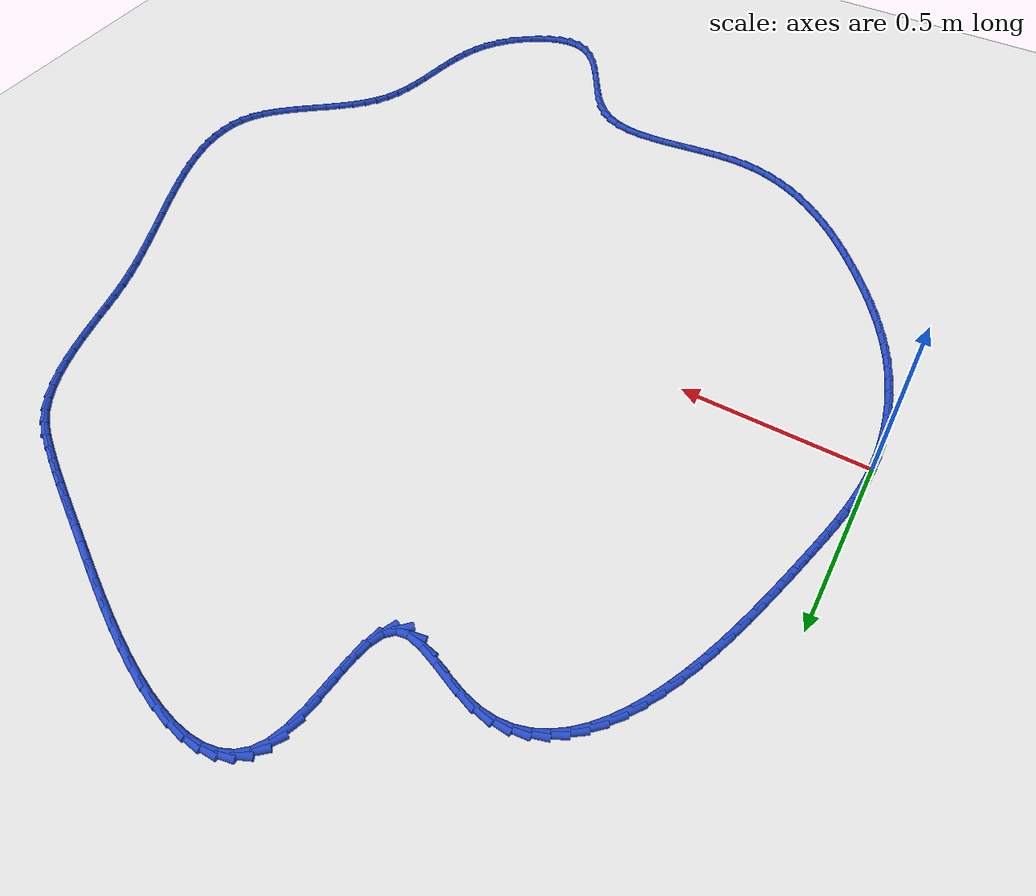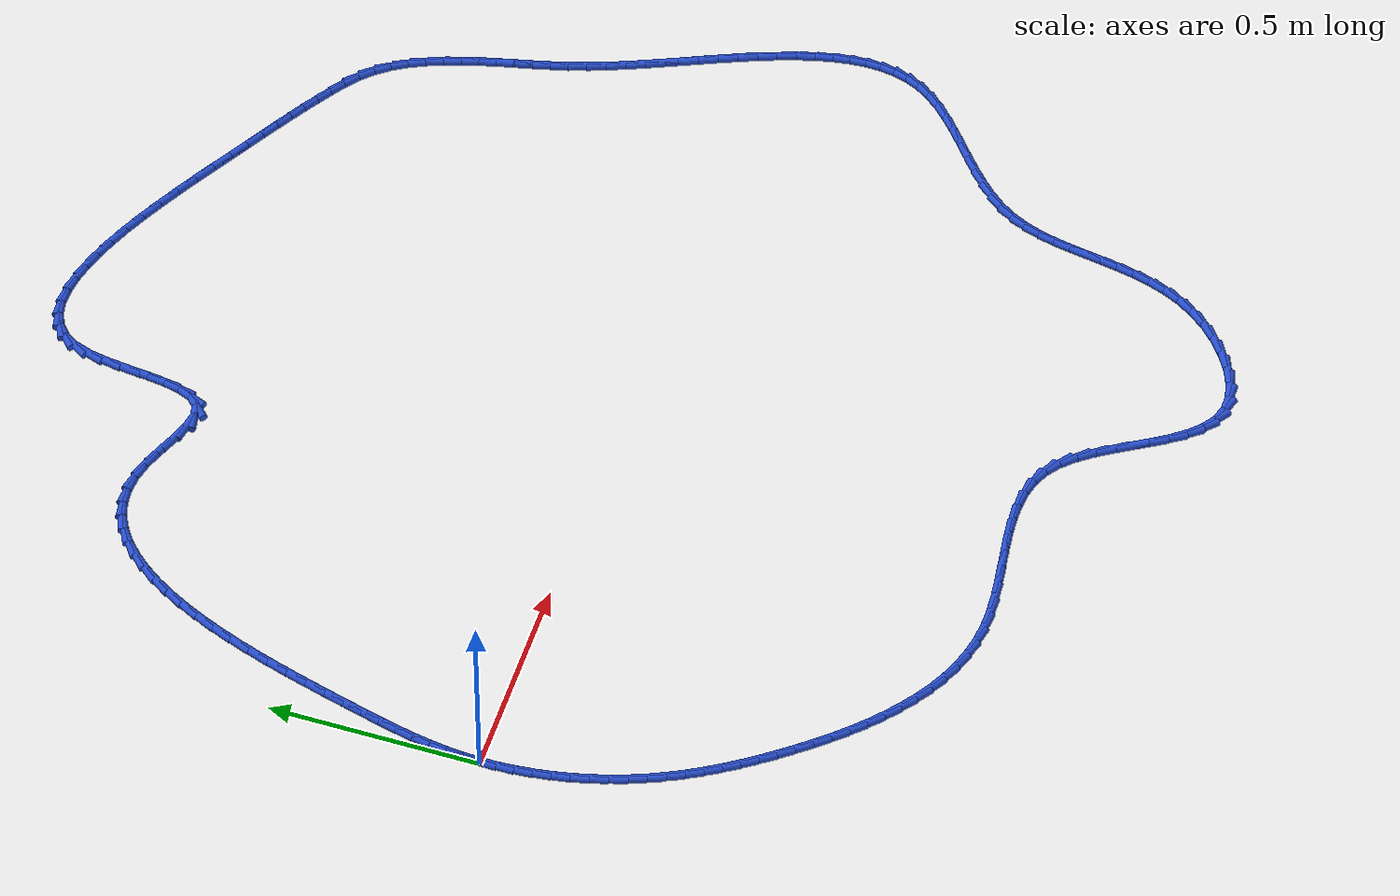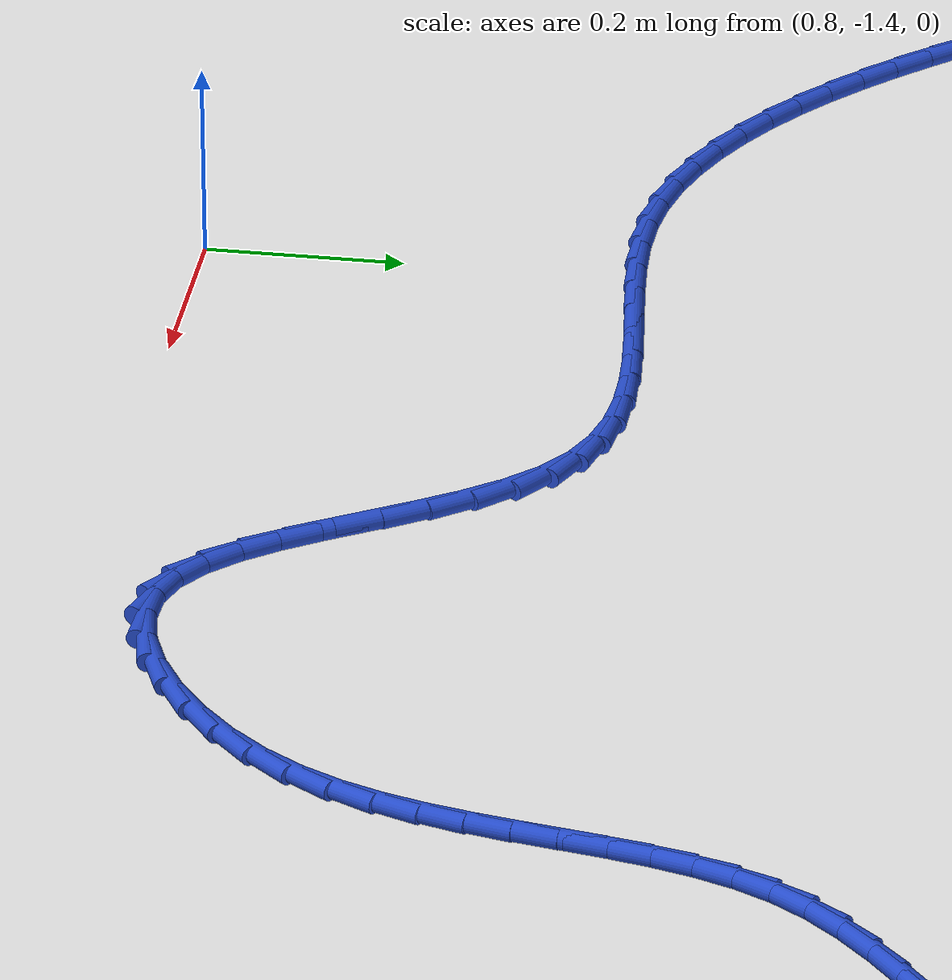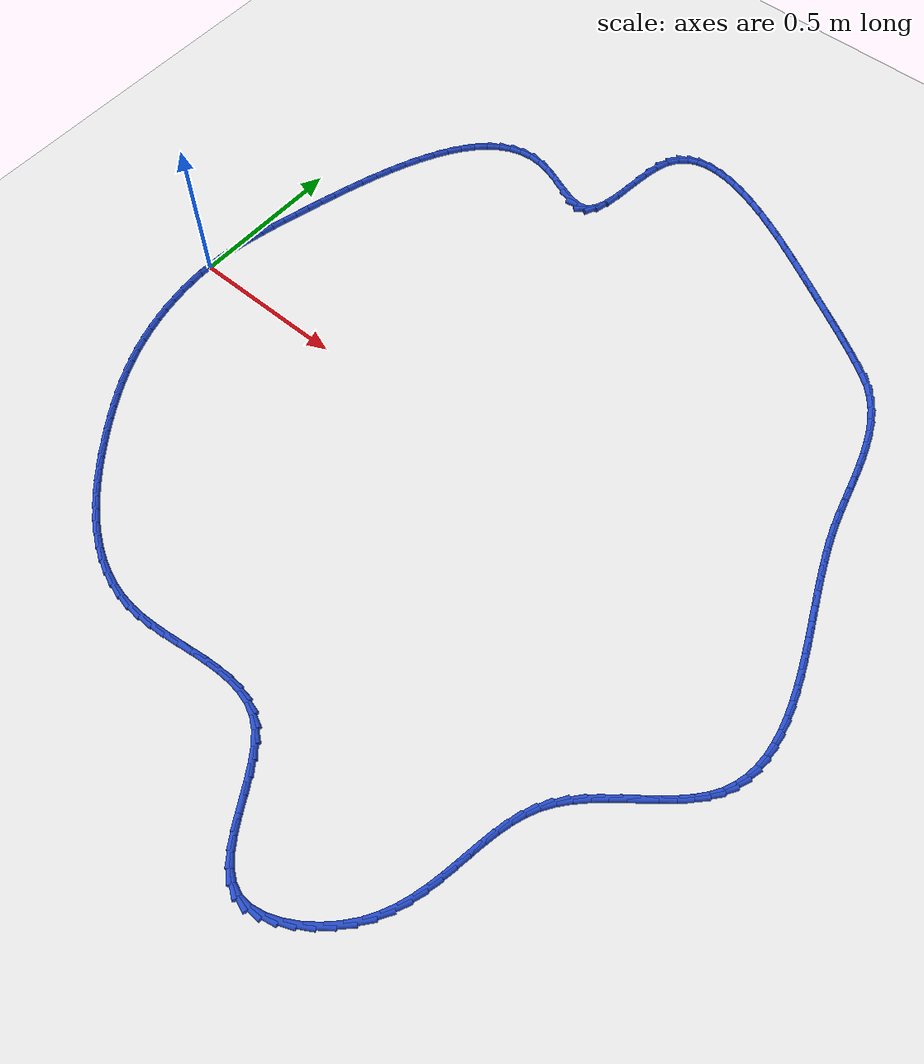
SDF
<sdf version="1.6">
 <world name="default">
  <light name="sun" type="directional">
   <pose>0 0 10 0 -0 0</pose>
   <diffuse>0.8 0.8 0.8 1</diffuse>
   <specular>0.2 0.2 0.2 1</specular>
   <attenuation>
    <range>1000</range>
    <constant>0.9</constant>
    <linear>0.01</linear>
    <quadratic>0.001</quadratic>
   </attenuation>
   <direction>-0.5 0.1 -0.9</direction>
  </light>
  <model name="ground_plane">
   <static>1</static>
   <link name="link">
    <collision name="collision">
     <geometry><plane><normal>0 0 1</normal><size>100 100</size></plane></geometry>
     <surface><friction><ode><mu>100</mu><mu2>50</mu2></ode></friction></surface>
    </collision>
    <visual name="visual">
     <cast_shadows>0</cast_shadows>
     <geometry><plane><normal>0 0 1</normal><size>100 100</size></plane></geometry>
     <material>
      <script><uri>file://media/materials/scripts/gazebo.material</uri><name>Gazebo/WhiteGlow</name></script>
     </material>
    </visual>
   </link>
  </model>
  <gravity>0 0 -9.8</gravity>
  <magnetic_field>6e-06 2.3e-05 -4.2e-05</magnetic_field>
  <atmosphere type="adiabatic"/>
  <physics name="default_physics" default="0" type="ode">
   <max_step_size>0.001</max_step_size>
   <real_time_factor>1</real_time_factor>
   <real_time_update_rate>1000</real_time_update_rate>
  </physics>
  <scene><ambient>0.4 0.4 0.4 1</ambient><background>0.7 0.7 0.7 1</background><shadows>1</shadows></scene>
  <spherical_coordinates>
   <surface_model>EARTH_WGS84</surface_model>
   <latitude_deg>0</latitude_deg>
   <longitude_deg>0</longitude_deg>
   <elevation>0</elevation>
   <heading_deg>0</heading_deg>
  </spherical_coordinates>
  <model name="line">
   <link name="link_0">
    <pose>-1.734723475976807e-18 -4.85722573273506e-17 0.01 0 1.57 1.528370388708105</pose>
    <collision name="collision">
     <geometry><cylinder><radius>0.01</radius><length>0.08</length></cylinder></geometry>
    </collision>
    <visual name="visual">
     <material>
      <script><name>Gazebo/Blue</name><uri>file://media/materials/scripts/gazebo.material</uri></script>
     </material>
     <geometry><cylinder><radius>0.01</radius><length>0.08</length></cylinder></geometry>
    </visual>
   </link>
   <link name="link_1">
    <pose>0.00172003753674495 0.040517793847105354 0.01 0 1.57 1.480477401472173</pose>
    <collision name="collision">
     <geometry><cylinder><radius>0.01</radius><length>0.08</length></cylinder></geometry>
    </collision>
    <visual name="visual">
     <material>
      <script><name>Gazebo/Blue</name><uri>file://media/materials/scripts/gazebo.material</uri></script>
     </material>
     <geometry><cylinder><radius>0.01</radius><length>0.08</length></cylinder></geometry>
    </visual>
   </link>
   <link name="link_2">
    <pose>0.0053483399748782134 0.08058061663351242 0.01 0 1.57 1.4373348506060561</pose>
    <collision name="collision">
     <geometry><cylinder><radius>0.01</radius><length>0.08</length></cylinder></geometry>
    </collision>
    <visual name="visual">
     <material>
      <script><name>Gazebo/Blue</name><uri>file://media/materials/scripts/gazebo.material</uri></script>
     </material>
     <geometry><cylinder><radius>0.01</radius><length>0.08</length></cylinder></geometry>
    </visual>
   </link>
   <link name="link_3">
    <pose>0.010715270375678139 0.1205549032725496 0.01 0 1.57 1.4001602886996463</pose>
    <collision name="collision">
     <geometry><cylinder><radius>0.01</radius><length>0.08</length></cylinder></geometry>
    </collision>
    <visual name="visual">
     <material>
      <script><name>Gazebo/Blue</name><uri>file://media/materials/scripts/gazebo.material</uri></script>
     </material>
     <geometry><cylinder><radius>0.01</radius><length>0.08</length></cylinder></geometry>
    </visual>
   </link>
   <link name="link_4">
    <pose>0.01765119180042307 0.1608070886775455 0.01 0 1.57 1.3697363426582096</pose>
    <collision name="collision">
     <geometry><cylinder><radius>0.01</radius><length>0.08</length></cylinder></geometry>
    </collision>
    <visual name="visual">
     <material>
      <script><name>Gazebo/Blue</name><uri>file://media/materials/scripts/gazebo.material</uri></script>
     </material>
     <geometry><cylinder><radius>0.01</radius><length>0.08</length></cylinder></geometry>
    </visual>
   </link>
   <link name="link_5">
    <pose>0.025986467310391337 0.2017036077618285 0.01 0 1.57 1.3463984910136473</pose>
    <collision name="collision">
     <geometry><cylinder><radius>0.01</radius><length>0.08</length></cylinder></geometry>
    </collision>
    <visual name="visual">
     <material>
      <script><name>Gazebo/Blue</name><uri>file://media/materials/scripts/gazebo.material</uri></script>
     </material>
     <geometry><cylinder><radius>0.01</radius><length>0.08</length></cylinder></geometry>
    </visual>
   </link>
   <link name="link_6">
    <pose>0.035551459966861286 0.2436108954387271 0.01 0 1.57 1.3300850885852846</pose>
    <collision name="collision">
     <geometry><cylinder><radius>0.01</radius><length>0.08</length></cylinder></geometry>
    </collision>
    <visual name="visual">
     <material>
      <script><name>Gazebo/Blue</name><uri>file://media/materials/scripts/gazebo.material</uri></script>
     </material>
     <geometry><cylinder><radius>0.01</radius><length>0.08</length></cylinder></geometry>
    </visual>
   </link>
   <link name="link_7">
    <pose>0.04617653283111127 0.28689538662156994 0.01 0 1.57 1.3204221853887352</pose>
    <collision name="collision">
     <geometry><cylinder><radius>0.01</radius><length>0.08</length></cylinder></geometry>
    </collision>
    <visual name="visual">
     <material>
      <script><name>Gazebo/Blue</name><uri>file://media/materials/scripts/gazebo.material</uri></script>
     </material>
     <geometry><cylinder><radius>0.01</radius><length>0.08</length></cylinder></geometry>
    </visual>
   </link>
   <link name="link_8">
    <pose>0.05769204896441961 0.3319235162236853 0.01 0 1.57 1.3160238211613218</pose>
    <collision name="collision">
     <geometry><cylinder><radius>0.01</radius><length>0.08</length></cylinder></geometry>
    </collision>
    <visual name="visual">
     <material>
      <script><name>Gazebo/Blue</name><uri>file://media/materials/scripts/gazebo.material</uri></script>
     </material>
     <geometry><cylinder><radius>0.01</radius><length>0.08</length></cylinder></geometry>
    </visual>
   </link>
   <link name="link_9">
    <pose>0.06994969291257157 0.378990127860714 0.01 0 1.57 1.3102897392908057</pose>
    <collision name="collision">
     <geometry><cylinder><radius>0.01</radius><length>0.08</length></cylinder></geometry>
    </collision>
    <visual name="visual">
     <material>
      <script><name>Gazebo/Blue</name><uri>file://media/materials/scripts/gazebo.material</uri></script>
     </material>
     <geometry><cylinder><radius>0.01</radius><length>0.08</length></cylinder></geometry>
    </visual>
   </link>
   <link name="link_10">
    <pose>0.08296831745633551 0.4278287631962327 0.01 0 1.57 1.3004733944327602</pose>
    <collision name="collision">
     <geometry><cylinder><radius>0.01</radius><length>0.08</length></cylinder></geometry>
    </collision>
    <visual name="visual">
     <material>
      <script><name>Gazebo/Blue</name><uri>file://media/materials/scripts/gazebo.material</uri></script>
     </material>
     <geometry><cylinder><radius>0.01</radius><length>0.08</length></cylinder></geometry>
    </visual>
   </link>
   <link name="link_11">
    <pose>0.09684562465601698 0.47790821111630843 0.01 0 1.57 1.2866186862908935</pose>
    <collision name="collision">
     <geometry><cylinder><radius>0.01</radius><length>0.08</length></cylinder></geometry>
    </collision>
    <visual name="visual">
     <material>
      <script><name>Gazebo/Blue</name><uri>file://media/materials/scripts/gazebo.material</uri></script>
     </material>
     <geometry><cylinder><radius>0.01</radius><length>0.08</length></cylinder></geometry>
    </visual>
   </link>
   <link name="link_12">
    <pose>0.11167978077608409 0.5286957018454448 0.01 0 1.57 1.2685675212239707</pose>
    <collision name="collision">
     <geometry><cylinder><radius>0.01</radius><length>0.08</length></cylinder></geometry>
    </collision>
    <visual name="visual">
     <material>
      <script><name>Gazebo/Blue</name><uri>file://media/materials/scripts/gazebo.material</uri></script>
     </material>
     <geometry><cylinder><radius>0.01</radius><length>0.08</length></cylinder></geometry>
    </visual>
   </link>
   <link name="link_13">
    <pose>0.127568952081005 0.5796584656081453 0.01 0 1.57 1.2459556664759364</pose>
    <collision name="collision">
     <geometry><cylinder><radius>0.01</radius><length>0.08</length></cylinder></geometry>
    </collision>
    <visual name="visual">
     <material>
      <script><name>Gazebo/Blue</name><uri>file://media/materials/scripts/gazebo.material</uri></script>
     </material>
     <geometry><cylinder><radius>0.01</radius><length>0.08</length></cylinder></geometry>
    </visual>
   </link>
   <link name="link_14">
    <pose>0.14461130483524764 0.6302637326289131 0.01 0 1.57 1.218201872596353</pose>
    <collision name="collision">
     <geometry><cylinder><radius>0.01</radius><length>0.08</length></cylinder></geometry>
    </collision>
    <visual name="visual">
     <material>
      <script><name>Gazebo/Blue</name><uri>file://media/materials/scripts/gazebo.material</uri></script>
     </material>
     <geometry><cylinder><radius>0.01</radius><length>0.08</length></cylinder></geometry>
    </visual>
   </link>
   <link name="link_15">
    <pose>0.1629050053032804 0.6799787331322517 0.01 0 1.57 1.1844764243952701</pose>
    <collision name="collision">
     <geometry><cylinder><radius>0.01</radius><length>0.08</length></cylinder></geometry>
    </collision>
    <visual name="visual">
     <material>
      <script><name>Gazebo/Blue</name><uri>file://media/materials/scripts/gazebo.material</uri></script>
     </material>
     <geometry><cylinder><radius>0.01</radius><length>0.08</length></cylinder></geometry>
    </visual>
   </link>
   <link name="link_16">
    <pose>0.18254821974957106 0.7282706973426643 0.01 0 1.57 1.1436501801805115</pose>
    <collision name="collision">
     <geometry><cylinder><radius>0.01</radius><length>0.08</length></cylinder></geometry>
    </collision>
    <visual name="visual">
     <material>
      <script><name>Gazebo/Blue</name><uri>file://media/materials/scripts/gazebo.material</uri></script>
     </material>
     <geometry><cylinder><radius>0.01</radius><length>0.08</length></cylinder></geometry>
    </visual>
   </link>
   <link name="link_17">
    <pose>0.20363911443858793 0.7746068554846547 0.01 0 1.57 1.0942257042189334</pose>
    <collision name="collision">
     <geometry><cylinder><radius>0.01</radius><length>0.08</length></cylinder></geometry>
    </collision>
    <visual name="visual">
     <material>
      <script><name>Gazebo/Blue</name><uri>file://media/materials/scripts/gazebo.material</uri></script>
     </material>
     <geometry><cylinder><radius>0.01</radius><length>0.08</length></cylinder></geometry>
    </visual>
   </link>
   <link name="link_18">
    <pose>0.22627585563479913 0.8184544377827263 0.01 0 1.57 1.0342578296235792</pose>
    <collision name="collision">
     <geometry><cylinder><radius>0.01</radius><length>0.08</length></cylinder></geometry>
    </collision>
    <visual name="visual">
     <material>
      <script><name>Gazebo/Blue</name><uri>file://media/materials/scripts/gazebo.material</uri></script>
     </material>
     <geometry><cylinder><radius>0.01</radius><length>0.08</length></cylinder></geometry>
    </visual>
   </link>
   <link name="link_19">
    <pose>0.2505566096026726 0.8592806744613821 0.01 0 1.57 0.9612877724573009</pose>
    <collision name="collision">
     <geometry><cylinder><radius>0.01</radius><length>0.08</length></cylinder></geometry>
    </collision>
    <visual name="visual">
     <material>
      <script><name>Gazebo/Blue</name><uri>file://media/materials/scripts/gazebo.material</uri></script>
     </material>
     <geometry><cylinder><radius>0.01</radius><length>0.08</length></cylinder></geometry>
    </visual>
   </link>
   <link name="link_20">
    <pose>0.2765795426066766 0.8965527957451256 0.01 0 1.57 0.8723542074193075</pose>
    <collision name="collision">
     <geometry><cylinder><radius>0.01</radius><length>0.08</length></cylinder></geometry>
    </collision>
    <visual name="visual">
     <material>
      <script><name>Gazebo/Blue</name><uri>file://media/materials/scripts/gazebo.material</uri></script>
     </material>
     <geometry><cylinder><radius>0.01</radius><length>0.08</length></cylinder></geometry>
    </visual>
   </link>
   <link name="link_21">
    <pose>0.3044428209112792 0.9297380318584604 0.01 0 1.57 0.7642215388143908</pose>
    <collision name="collision">
     <geometry><cylinder><radius>0.01</radius><length>0.08</length></cylinder></geometry>
    </collision>
    <visual name="visual">
     <material>
      <script><name>Gazebo/Blue</name><uri>file://media/materials/scripts/gazebo.material</uri></script>
     </material>
     <geometry><cylinder><radius>0.01</radius><length>0.08</length></cylinder></geometry>
    </visual>
   </link>
   <link name="link_22">
    <pose>0.33424461078094847 0.95830361302589 0.01 0 1.57 0.6340740596291115</pose>
    <collision name="collision">
     <geometry><cylinder><radius>0.01</radius><length>0.08</length></cylinder></geometry>
    </collision>
    <visual name="visual">
     <material>
      <script><name>Gazebo/Blue</name><uri>file://media/materials/scripts/gazebo.material</uri></script>
     </material>
     <geometry><cylinder><radius>0.01</radius><length>0.08</length></cylinder></geometry>
    </visual>
   </link>
   <link name="link_23">
    <pose>0.36608307848015265 0.9817167694719173 0.01 0 1.57 0.48095103829503133</pose>
    <collision name="collision">
     <geometry><cylinder><radius>0.01</radius><length>0.08</length></cylinder></geometry>
    </collision>
    <visual name="visual">
     <material>
      <script><name>Gazebo/Blue</name><uri>file://media/materials/scripts/gazebo.material</uri></script>
     </material>
     <geometry><cylinder><radius>0.01</radius><length>0.08</length></cylinder></geometry>
    </visual>
   </link>
   <link name="link_24">
    <pose>0.40005639027335943 0.999444731421046 0.01 0 1.57 0.30779704752823633</pose>
    <collision name="collision">
     <geometry><cylinder><radius>0.01</radius><length>0.08</length></cylinder></geometry>
    </collision>
    <visual name="visual">
     <material>
      <script><name>Gazebo/Blue</name><uri>file://media/materials/scripts/gazebo.material</uri></script>
     </material>
     <geometry><cylinder><radius>0.01</radius><length>0.08</length></cylinder></geometry>
    </visual>
   </link>
   <link name="link_25">
    <pose>0.43626271242503745 1.0109547290977796 0.01 0 1.57 0.12287479742818654</pose>
    <collision name="collision">
     <geometry><cylinder><radius>0.01</radius><length>0.08</length></cylinder></geometry>
    </collision>
    <visual name="visual">
     <material>
      <script><name>Gazebo/Blue</name><uri>file://media/materials/scripts/gazebo.material</uri></script>
     </material>
     <geometry><cylinder><radius>0.01</radius><length>0.08</length></cylinder></geometry>
    </visual>
   </link>
   <link name="link_26">
    <pose>0.47480021119965465 1.0157139927266214 0.01 0 1.57 -0.06153886480215298</pose>
    <collision name="collision">
     <geometry><cylinder><radius>0.01</radius><length>0.08</length></cylinder></geometry>
    </collision>
    <visual name="visual">
     <material>
      <script><name>Gazebo/Blue</name><uri>file://media/materials/scripts/gazebo.material</uri></script>
     </material>
     <geometry><cylinder><radius>0.01</radius><length>0.08</length></cylinder></geometry>
    </visual>
   </link>
   <link name="link_27">
    <pose>0.5157670528616787 1.013189752532075 0.01 0 1.57 -0.23293348251479826</pose>
    <collision name="collision">
     <geometry><cylinder><radius>0.01</radius><length>0.08</length></cylinder></geometry>
    </collision>
    <visual name="visual">
     <material>
      <script><name>Gazebo/Blue</name><uri>file://media/materials/scripts/gazebo.material</uri></script>
     </material>
     <geometry><cylinder><radius>0.01</radius><length>0.08</length></cylinder></geometry>
    </visual>
   </link>
   <link name="link_28">
    <pose>0.559250366901823 1.0028737796666098 0.01 0 1.57 -0.3540604103288939</pose>
    <collision name="collision">
     <geometry><cylinder><radius>0.01</radius><length>0.08</length></cylinder></geometry>
    </collision>
    <visual name="visual">
     <material>
      <script><name>Gazebo/Blue</name><uri>file://media/materials/scripts/gazebo.material</uri></script>
     </material>
     <geometry><cylinder><radius>0.01</radius><length>0.08</length></cylinder></geometry>
    </visual>
   </link>
   <link name="link_29">
    <pose>0.6044847584894163 0.9861534842098224 0.01 0 1.57 -0.39229845676426855</pose>
    <collision name="collision">
     <geometry><cylinder><radius>0.01</radius><length>0.08</length></cylinder></geometry>
    </collision>
    <visual name="visual">
     <material>
      <script><name>Gazebo/Blue</name><uri>file://media/materials/scripts/gazebo.material</uri></script>
     </material>
     <geometry><cylinder><radius>0.01</radius><length>0.08</length></cylinder></geometry>
    </visual>
   </link>
   <link name="link_30">
    <pose>0.6492605328503174 0.9676277637339419 0.01 0 1.57 -0.3521428855583303</pose>
    <collision name="collision">
     <geometry><cylinder><radius>0.01</radius><length>0.08</length></cylinder></geometry>
    </collision>
    <visual name="visual">
     <material>
      <script><name>Gazebo/Blue</name><uri>file://media/materials/scripts/gazebo.material</uri></script>
     </material>
     <geometry><cylinder><radius>0.01</radius><length>0.08</length></cylinder></geometry>
    </visual>
   </link>
   <link name="link_31">
    <pose>0.6912281915806306 0.9522063775614948 0.01 0 1.57 -0.19857816127370922</pose>
    <collision name="collision">
     <geometry><cylinder><radius>0.01</radius><length>0.08</length></cylinder></geometry>
    </collision>
    <visual name="visual">
     <material>
      <script><name>Gazebo/Blue</name><uri>file://media/materials/scripts/gazebo.material</uri></script>
     </material>
     <geometry><cylinder><radius>0.01</radius><length>0.08</length></cylinder></geometry>
    </visual>
   </link>
   <link name="link_32">
    <pose>0.7280382362764611 0.9447990850150074 0.01 0 1.57 0.185271720738517</pose>
    <collision name="collision">
     <geometry><cylinder><radius>0.01</radius><length>0.08</length></cylinder></geometry>
    </collision>
    <visual name="visual">
     <material>
      <script><name>Gazebo/Blue</name><uri>file://media/materials/scripts/gazebo.material</uri></script>
     </material>
     <geometry><cylinder><radius>0.01</radius><length>0.08</length></cylinder></geometry>
    </visual>
   </link>
   <link name="link_33">
    <pose>0.7573529104168982 0.9502932732521467 0.01 0 1.57 0.7816259062802736</pose>
    <collision name="collision">
     <geometry><cylinder><radius>0.01</radius><length>0.08</length></cylinder></geometry>
    </collision>
    <visual name="visual">
     <material>
      <script><name>Gazebo/Blue</name><uri>file://media/materials/scripts/gazebo.material</uri></script>
     </material>
     <geometry><cylinder><radius>0.01</radius><length>0.08</length></cylinder></geometry>
    </visual>
   </link>
   <link name="link_34">
    <pose>0.7781968417413209 0.9709805374854211 0.01 0 1.57 1.1712888422678254</pose>
    <collision name="collision">
     <geometry><cylinder><radius>0.01</radius><length>0.08</length></cylinder></geometry>
    </collision>
    <visual name="visual">
     <material>
      <script><name>Gazebo/Blue</name><uri>file://media/materials/scripts/gazebo.material</uri></script>
     </material>
     <geometry><cylinder><radius>0.01</radius><length>0.08</length></cylinder></geometry>
    </visual>
   </link>
   <link name="link_35">
    <pose>0.792209776385435 1.0041698087358348 0.01 0 1.57 1.3591513011999974</pose>
    <collision name="collision">
     <geometry><cylinder><radius>0.01</radius><length>0.08</length></cylinder></geometry>
    </collision>
    <visual name="visual">
     <material>
      <script><name>Gazebo/Blue</name><uri>file://media/materials/scripts/gazebo.material</uri></script>
     </material>
     <geometry><cylinder><radius>0.01</radius><length>0.08</length></cylinder></geometry>
    </visual>
   </link>
   <link name="link_36">
    <pose>0.801327661819899 1.0466056566604007 0.01 0 1.57 1.4442987302547403</pose>
    <collision name="collision">
     <geometry><cylinder><radius>0.01</radius><length>0.08</length></cylinder></geometry>
    </collision>
    <visual name="visual">
     <material>
      <script><name>Gazebo/Blue</name><uri>file://media/materials/scripts/gazebo.material</uri></script>
     </material>
     <geometry><cylinder><radius>0.01</radius><length>0.08</length></cylinder></geometry>
    </visual>
   </link>
   <link name="link_37">
    <pose>0.8074864455153722 1.0950326509161312 0.01 0 1.57 1.4707530652104115</pose>
    <collision name="collision">
     <geometry><cylinder><radius>0.01</radius><length>0.08</length></cylinder></geometry>
    </collision>
    <visual name="visual">
     <material>
      <script><name>Gazebo/Blue</name><uri>file://media/materials/scripts/gazebo.material</uri></script>
     </material>
     <geometry><cylinder><radius>0.01</radius><length>0.08</length></cylinder></geometry>
    </visual>
   </link>
   <link name="link_38">
    <pose>0.8126220749425132 1.146195361160038 0.01 0 1.57 1.451926823432549</pose>
    <collision name="collision">
     <geometry><cylinder><radius>0.01</radius><length>0.08</length></cylinder></geometry>
    </collision>
    <visual name="visual">
     <material>
      <script><name>Gazebo/Blue</name><uri>file://media/materials/scripts/gazebo.material</uri></script>
     </material>
     <geometry><cylinder><radius>0.01</radius><length>0.08</length></cylinder></geometry>
    </visual>
   </link>
   <link name="link_39">
    <pose>0.8186704975719811 1.196838357049134 0.01 0 1.57 1.3831935378688356</pose>
    <collision name="collision">
     <geometry><cylinder><radius>0.01</radius><length>0.08</length></cylinder></geometry>
    </collision>
    <visual name="visual">
     <material>
      <script><name>Gazebo/Blue</name><uri>file://media/materials/scripts/gazebo.material</uri></script>
     </material>
     <geometry><cylinder><radius>0.01</radius><length>0.08</length></cylinder></geometry>
    </visual>
   </link>
   <link name="link_40">
    <pose>0.8275676608744351 1.2437062082404324 0.01 0 1.57 1.2401859303522513</pose>
    <collision name="collision">
     <geometry><cylinder><radius>0.01</radius><length>0.08</length></cylinder></geometry>
    </collision>
    <visual name="visual">
     <material>
      <script><name>Gazebo/Blue</name><uri>file://media/materials/scripts/gazebo.material</uri></script>
     </material>
     <geometry><cylinder><radius>0.01</radius><length>0.08</length></cylinder></geometry>
    </visual>
   </link>
   <link name="link_41">
    <pose>0.8412434088824086 1.2835531437496128 0.01 0 1.57 1.0040865140780024</pose>
    <collision name="collision">
     <geometry><cylinder><radius>0.01</radius><length>0.08</length></cylinder></geometry>
    </collision>
    <visual name="visual">
     <material>
      <script><name>Gazebo/Blue</name><uri>file://media/materials/scripts/gazebo.material</uri></script>
     </material>
     <geometry><cylinder><radius>0.01</radius><length>0.08</length></cylinder></geometry>
    </visual>
   </link>
   <link name="link_42">
    <pose>0.8608497418289937 1.3143644155162704 0.01 0 1.57 0.7227316140498389</pose>
    <collision name="collision">
     <geometry><cylinder><radius>0.01</radius><length>0.08</length></cylinder></geometry>
    </collision>
    <visual name="visual">
     <material>
      <script><name>Gazebo/Blue</name><uri>file://media/materials/scripts/gazebo.material</uri></script>
     </material>
     <geometry><cylinder><radius>0.01</radius><length>0.08</length></cylinder></geometry>
    </visual>
   </link>
   <link name="link_43">
    <pose>0.8860063430584073 1.3365503346220229 0.01 0 1.57 0.4416688211667742</pose>
    <collision name="collision">
     <geometry><cylinder><radius>0.01</radius><length>0.08</length></cylinder></geometry>
    </collision>
    <visual name="visual">
     <material>
      <script><name>Gazebo/Blue</name><uri>file://media/materials/scripts/gazebo.material</uri></script>
     </material>
     <geometry><cylinder><radius>0.01</radius><length>0.08</length></cylinder></geometry>
    </visual>
   </link>
   <link name="link_44">
    <pose>0.9161537859186416 1.350804673315645 0.01 0 1.57 0.20019579997016396</pose>
    <collision name="collision">
     <geometry><cylinder><radius>0.01</radius><length>0.08</length></cylinder></geometry>
    </collision>
    <visual name="visual">
     <material>
      <script><name>Gazebo/Blue</name><uri>file://media/materials/scripts/gazebo.material</uri></script>
     </material>
     <geometry><cylinder><radius>0.01</radius><length>0.08</length></cylinder></geometry>
    </visual>
   </link>
   <link name="link_45">
    <pose>0.95073264375769 1.3578212038459103 0.01 0 1.57 0.012287657683713354</pose>
    <collision name="collision">
     <geometry><cylinder><radius>0.01</radius><length>0.08</length></cylinder></geometry>
    </collision>
    <visual name="visual">
     <material>
      <script><name>Gazebo/Blue</name><uri>file://media/materials/scripts/gazebo.material</uri></script>
     </material>
     <geometry><cylinder><radius>0.01</radius><length>0.08</length></cylinder></geometry>
    </visual>
   </link>
   <link name="link_46">
    <pose>0.9891834899235449 1.3582936984615925 0.01 0 1.57 -0.12806278332758594</pose>
    <collision name="collision">
     <geometry><cylinder><radius>0.01</radius><length>0.08</length></cylinder></geometry>
    </collision>
    <visual name="visual">
     <material>
      <script><name>Gazebo/Blue</name><uri>file://media/materials/scripts/gazebo.material</uri></script>
     </material>
     <geometry><cylinder><radius>0.01</radius><length>0.08</length></cylinder></geometry>
    </visual>
   </link>
   <link name="link_47">
    <pose>1.0309468977641985 1.3529159294114659 0.01 0 1.57 -0.23236270712452842</pose>
    <collision name="collision">
     <geometry><cylinder><radius>0.01</radius><length>0.08</length></cylinder></geometry>
    </collision>
    <visual name="visual">
     <material>
      <script><name>Gazebo/Blue</name><uri>file://media/materials/scripts/gazebo.material</uri></script>
     </material>
     <geometry><cylinder><radius>0.01</radius><length>0.08</length></cylinder></geometry>
    </visual>
   </link>
   <link name="link_48">
    <pose>1.0754634406276435 1.3423816689443036 0.01 0 1.57 -0.3106678040880698</pose>
    <collision name="collision">
     <geometry><cylinder><radius>0.01</radius><length>0.08</length></cylinder></geometry>
    </collision>
    <visual name="visual">
     <material>
      <script><name>Gazebo/Blue</name><uri>file://media/materials/scripts/gazebo.material</uri></script>
     </material>
     <geometry><cylinder><radius>0.01</radius><length>0.08</length></cylinder></geometry>
    </visual>
   </link>
   <link name="link_49">
    <pose>1.1221736918618737 1.3273846893088799 0.01 0 1.57 -0.3702672116930253</pose>
    <collision name="collision">
     <geometry><cylinder><radius>0.01</radius><length>0.08</length></cylinder></geometry>
    </collision>
    <visual name="visual">
     <material>
      <script><name>Gazebo/Blue</name><uri>file://media/materials/scripts/gazebo.material</uri></script>
     </material>
     <geometry><cylinder><radius>0.01</radius><length>0.08</length></cylinder></geometry>
    </visual>
   </link>
   <link name="link_50">
    <pose>1.1705182248148807 1.3086187627539687 0.01 0 1.57 -0.41614284398418394</pose>
    <collision name="collision">
     <geometry><cylinder><radius>0.01</radius><length>0.08</length></cylinder></geometry>
    </collision>
    <visual name="visual">
     <material>
      <script><name>Gazebo/Blue</name><uri>file://media/materials/scripts/gazebo.material</uri></script>
     </material>
     <geometry><cylinder><radius>0.01</radius><length>0.08</length></cylinder></geometry>
    </visual>
   </link>
   <link name="link_51">
    <pose>1.2199376128346577 1.286777661528344 0.01 0 1.57 -0.4516425165832345</pose>
    <collision name="collision">
     <geometry><cylinder><radius>0.01</radius><length>0.08</length></cylinder></geometry>
    </collision>
    <visual name="visual">
     <material>
      <script><name>Gazebo/Blue</name><uri>file://media/materials/scripts/gazebo.material</uri></script>
     </material>
     <geometry><cylinder><radius>0.01</radius><length>0.08</length></cylinder></geometry>
    </visual>
   </link>
   <link name="link_52">
    <pose>1.2698724292691974 1.2625551578807788 0.01 0 1.57 -0.4789970460326138</pose>
    <collision name="collision">
     <geometry><cylinder><radius>0.01</radius><length>0.08</length></cylinder></geometry>
    </collision>
    <visual name="visual">
     <material>
      <script><name>Gazebo/Blue</name><uri>file://media/materials/scripts/gazebo.material</uri></script>
     </material>
     <geometry><cylinder><radius>0.01</radius><length>0.08</length></cylinder></geometry>
    </visual>
   </link>
   <link name="link_53">
    <pose>1.3197632474664915 1.2366450240600475 0.01 0 1.57 -0.4996587653629642</pose>
    <collision name="collision">
     <geometry><cylinder><radius>0.01</radius><length>0.08</length></cylinder></geometry>
    </collision>
    <visual name="visual">
     <material>
      <script><name>Gazebo/Blue</name><uri>file://media/materials/scripts/gazebo.material</uri></script>
     </material>
     <geometry><cylinder><radius>0.01</radius><length>0.08</length></cylinder></geometry>
    </visual>
   </link>
   <link name="link_54">
    <pose>1.3690506407745338 1.209741032314924 0.01 0 1.57 -0.5145024851336627</pose>
    <collision name="collision">
     <geometry><cylinder><radius>0.01</radius><length>0.08</length></cylinder></geometry>
    </collision>
    <visual name="visual">
     <material>
      <script><name>Gazebo/Blue</name><uri>file://media/materials/scripts/gazebo.material</uri></script>
     </material>
     <geometry><cylinder><radius>0.01</radius><length>0.08</length></cylinder></geometry>
    </visual>
   </link>
   <link name="link_55">
    <pose>1.4171751825413168 1.1825369548941815 0.01 0 1.57 -0.5239224840192971</pose>
    <collision name="collision">
     <geometry><cylinder><radius>0.01</radius><length>0.08</length></cylinder></geometry>
    </collision>
    <visual name="visual">
     <material>
      <script><name>Gazebo/Blue</name><uri>file://media/materials/scripts/gazebo.material</uri></script>
     </material>
     <geometry><cylinder><radius>0.01</radius><length>0.08</length></cylinder></geometry>
    </visual>
   </link>
   <link name="link_56">
    <pose>1.4635774461148325 1.155726564046595 0.01 0 1.57 -0.5278366400154734</pose>
    <collision name="collision">
     <geometry><cylinder><radius>0.01</radius><length>0.08</length></cylinder></geometry>
    </collision>
    <visual name="visual">
     <material>
      <script><name>Gazebo/Blue</name><uri>file://media/materials/scripts/gazebo.material</uri></script>
     </material>
     <geometry><cylinder><radius>0.01</radius><length>0.08</length></cylinder></geometry>
    </visual>
   </link>
   <link name="link_57">
    <pose>1.5076980048430744 1.1300036320209375 0.01 0 1.57 -0.5265794143272406</pose>
    <collision name="collision">
     <geometry><cylinder><radius>0.01</radius><length>0.08</length></cylinder></geometry>
    </collision>
    <visual name="visual">
     <material>
      <script><name>Gazebo/Blue</name><uri>file://media/materials/scripts/gazebo.material</uri></script>
     </material>
     <geometry><cylinder><radius>0.01</radius><length>0.08</length></cylinder></geometry>
    </visual>
   </link>
   <link name="link_58">
    <pose>1.5490832293368813 1.105945104968783 0.01 0 1.57 -0.5259906616675976</pose>
    <collision name="collision">
     <geometry><cylinder><radius>0.01</radius><length>0.08</length></cylinder></geometry>
    </collision>
    <visual name="visual">
     <material>
      <script><name>Gazebo/Blue</name><uri>file://media/materials/scripts/gazebo.material</uri></script>
     </material>
     <geometry><cylinder><radius>0.01</radius><length>0.08</length></cylinder></geometry>
    </visual>
   </link>
   <link name="link_59">
    <pose>1.5879619960227718 1.0833742754157263 0.01 0 1.57 -0.5290911237635645</pose>
    <collision name="collision">
     <geometry><cylinder><radius>0.01</radius><length>0.08</length></cylinder></geometry>
    </collision>
    <visual name="visual">
     <material>
      <script><name>Gazebo/Blue</name><uri>file://media/materials/scripts/gazebo.material</uri></script>
     </material>
     <geometry><cylinder><radius>0.01</radius><length>0.08</length></cylinder></geometry>
    </visual>
   </link>
   <link name="link_60">
    <pose>1.6248340999521775 1.0618152753537555 0.01 0 1.57 -0.5363395498818827</pose>
    <collision name="collision">
     <geometry><cylinder><radius>0.01</radius><length>0.08</length></cylinder></geometry>
    </collision>
    <visual name="visual">
     <material>
      <script><name>Gazebo/Blue</name><uri>file://media/materials/scripts/gazebo.material</uri></script>
     </material>
     <geometry><cylinder><radius>0.01</radius><length>0.08</length></cylinder></geometry>
    </visual>
   </link>
   <link name="link_61">
    <pose>1.6602000208503986 1.0407914807271699 0.01 0 1.57 -0.547856251935626</pose>
    <collision name="collision">
     <geometry><cylinder><radius>0.01</radius><length>0.08</length></cylinder></geometry>
    </collision>
    <visual name="visual">
     <material>
      <script><name>Gazebo/Blue</name><uri>file://media/materials/scripts/gazebo.material</uri></script>
     </material>
     <geometry><cylinder><radius>0.01</radius><length>0.08</length></cylinder></geometry>
    </visual>
   </link>
   <link name="link_62">
    <pose>1.6945602384427365 1.0198262674802678 0.01 0 1.57 -0.563340637267597</pose>
    <collision name="collision">
     <geometry><cylinder><radius>0.01</radius><length>0.08</length></cylinder></geometry>
    </collision>
    <visual name="visual">
     <material>
      <script><name>Gazebo/Blue</name><uri>file://media/materials/scripts/gazebo.material</uri></script>
     </material>
     <geometry><cylinder><radius>0.01</radius><length>0.08</length></cylinder></geometry>
    </visual>
   </link>
   <link name="link_63">
    <pose>1.7284152324544921 0.998443011557348 0.01 0 1.57 -0.5820704813350454</pose>
    <collision name="collision">
     <geometry><cylinder><radius>0.01</radius><length>0.08</length></cylinder></geometry>
    </collision>
    <visual name="visual">
     <material>
      <script><name>Gazebo/Blue</name><uri>file://media/materials/scripts/gazebo.material</uri></script>
     </material>
     <geometry><cylinder><radius>0.01</radius><length>0.08</length></cylinder></geometry>
    </visual>
   </link>
   <link name="link_64">
    <pose>1.7622654826109647 0.9761650889027098 0.01 0 1.57 -0.6043241248962135</pose>
    <collision name="collision">
     <geometry><cylinder><radius>0.01</radius><length>0.08</length></cylinder></geometry>
    </collision>
    <visual name="visual">
     <material>
      <script><name>Gazebo/Blue</name><uri>file://media/materials/scripts/gazebo.material</uri></script>
     </material>
     <geometry><cylinder><radius>0.01</radius><length>0.08</length></cylinder></geometry>
    </visual>
   </link>
   <link name="link_65">
    <pose>1.796547776417198 0.9524930386943633 0.01 0 1.57 -0.6675204363629734</pose>
    <collision name="collision">
     <geometry><cylinder><radius>0.01</radius><length>0.08</length></cylinder></geometry>
    </collision>
    <visual name="visual">
     <material>
      <script><name>Gazebo/Blue</name><uri>file://media/materials/scripts/gazebo.material</uri></script>
     </material>
     <geometry><cylinder><radius>0.01</radius><length>0.08</length></cylinder></geometry>
    </visual>
   </link>
   <link name="link_66">
    <pose>1.8298315792274327 0.9262578740776198 0.01 0 1.57 -0.8004527332438622</pose>
    <collision name="collision">
     <geometry><cylinder><radius>0.01</radius><length>0.08</length></cylinder></geometry>
    </collision>
    <visual name="visual">
     <material>
      <script><name>Gazebo/Blue</name><uri>file://media/materials/scripts/gazebo.material</uri></script>
     </material>
     <geometry><cylinder><radius>0.01</radius><length>0.08</length></cylinder></geometry>
    </visual>
   </link>
   <link name="link_67">
    <pose>1.8592201055356996 0.8959708907651681 0.01 0 1.57 -0.9324349996659546</pose>
    <collision name="collision">
     <geometry><cylinder><radius>0.01</radius><length>0.08</length></cylinder></geometry>
    </collision>
    <visual name="visual">
     <material>
      <script><name>Gazebo/Blue</name><uri>file://media/materials/scripts/gazebo.material</uri></script>
     </material>
     <geometry><cylinder><radius>0.01</radius><length>0.08</length></cylinder></geometry>
    </visual>
   </link>
   <link name="link_68">
    <pose>1.8844590196599926 0.8619561752817791 0.01 0 1.57 -1.0424098730874778</pose>
    <collision name="collision">
     <geometry><cylinder><radius>0.01</radius><length>0.08</length></cylinder></geometry>
    </collision>
    <visual name="visual">
     <material>
      <script><name>Gazebo/Blue</name><uri>file://media/materials/scripts/gazebo.material</uri></script>
     </material>
     <geometry><cylinder><radius>0.01</radius><length>0.08</length></cylinder></geometry>
    </visual>
   </link>
   <link name="link_69">
    <pose>1.9060179107494193 0.825024556234662 0.01 0 1.57 -1.1314198093086925</pose>
    <collision name="collision">
     <geometry><cylinder><radius>0.01</radius><length>0.08</length></cylinder></geometry>
    </collision>
    <visual name="visual">
     <material>
      <script><name>Gazebo/Blue</name><uri>file://media/materials/scripts/gazebo.material</uri></script>
     </material>
     <geometry><cylinder><radius>0.01</radius><length>0.08</length></cylinder></geometry>
    </visual>
   </link>
   <link name="link_70">
    <pose>1.9243663709442456 0.7859868642421773 0.01 0 1.57 -1.2015732324244608</pose>
    <collision name="collision">
     <geometry><cylinder><radius>0.01</radius><length>0.08</length></cylinder></geometry>
    </collision>
    <visual name="visual">
     <material>
      <script><name>Gazebo/Blue</name><uri>file://media/materials/scripts/gazebo.material</uri></script>
     </material>
     <geometry><cylinder><radius>0.01</radius><length>0.08</length></cylinder></geometry>
    </visual>
   </link>
   <link name="link_71">
    <pose>1.9399739923847379 0.7456539299226854 0.01 0 1.57 -1.2549977677668878</pose>
    <collision name="collision">
     <geometry><cylinder><radius>0.01</radius><length>0.08</length></cylinder></geometry>
    </collision>
    <visual name="visual">
     <material>
      <script><name>Gazebo/Blue</name><uri>file://media/materials/scripts/gazebo.material</uri></script>
     </material>
     <geometry><cylinder><radius>0.01</radius><length>0.08</length></cylinder></geometry>
    </visual>
   </link>
   <link name="link_72">
    <pose>1.9533103672111614 0.7048365838945472 0.01 0 1.57 -1.2939347123748994</pose>
    <collision name="collision">
     <geometry><cylinder><radius>0.01</radius><length>0.08</length></cylinder></geometry>
    </collision>
    <visual name="visual">
     <material>
      <script><name>Gazebo/Blue</name><uri>file://media/materials/scripts/gazebo.material</uri></script>
     </material>
     <geometry><cylinder><radius>0.01</radius><length>0.08</length></cylinder></geometry>
    </visual>
   </link>
   <link name="link_73">
    <pose>1.9648606393434667 0.6641894380447444 0.01 0 1.57 -1.3212524495131095</pose>
    <collision name="collision">
     <geometry><cylinder><radius>0.01</radius><length>0.08</length></cylinder></geometry>
    </collision>
    <visual name="visual">
     <material>
      <script><name>Gazebo/Blue</name><uri>file://media/materials/scripts/gazebo.material</uri></script>
     </material>
     <geometry><cylinder><radius>0.01</radius><length>0.08</length></cylinder></geometry>
    </visual>
   </link>
   <link name="link_74">
    <pose>1.975174276395801 0.6237209681839548 0.01 0 1.57 -1.3367598033457073</pose>
    <collision name="collision">
     <geometry><cylinder><radius>0.01</radius><length>0.08</length></cylinder></geometry>
    </collision>
    <visual name="visual">
     <material>
      <script><name>Gazebo/Blue</name><uri>file://media/materials/scripts/gazebo.material</uri></script>
     </material>
     <geometry><cylinder><radius>0.01</radius><length>0.08</length></cylinder></geometry>
    </visual>
   </link>
   <link name="link_75">
    <pose>1.9848173739300197 0.5832726212072354 0.01 0 1.57 -1.339966599983334</pose>
    <collision name="collision">
     <geometry><cylinder><radius>0.01</radius><length>0.08</length></cylinder></geometry>
    </collision>
    <visual name="visual">
     <material>
      <script><name>Gazebo/Blue</name><uri>file://media/materials/scripts/gazebo.material</uri></script>
     </material>
     <geometry><cylinder><radius>0.01</radius><length>0.08</length></cylinder></geometry>
    </visual>
   </link>
   <link name="link_76">
    <pose>1.9943560275302878 0.5426858437855591 0.01 0 1.57 -1.330903270635454</pose>
    <collision name="collision">
     <geometry><cylinder><radius>0.01</radius><length>0.08</length></cylinder></geometry>
    </collision>
    <visual name="visual">
     <material>
      <script><name>Gazebo/Blue</name><uri>file://media/materials/scripts/gazebo.material</uri></script>
     </material>
     <geometry><cylinder><radius>0.01</radius><length>0.08</length></cylinder></geometry>
    </visual>
   </link>
   <link name="link_77">
    <pose>2.00435633278077 0.5018020825898984 0.01 0 1.57 -1.3100981899154562</pose>
    <collision name="collision">
     <geometry><cylinder><radius>0.01</radius><length>0.08</length></cylinder></geometry>
    </collision>
    <visual name="visual">
     <material>
      <script><name>Gazebo/Blue</name><uri>file://media/materials/scripts/gazebo.material</uri></script>
     </material>
     <geometry><cylinder><radius>0.01</radius><length>0.08</length></cylinder></geometry>
    </visual>
   </link>
   <link name="link_78">
    <pose>2.0153843852656297 0.46046278429122733 0.01 0 1.57 -1.2785554112859177</pose>
    <collision name="collision">
     <geometry><cylinder><radius>0.01</radius><length>0.08</length></cylinder></geometry>
    </collision>
    <visual name="visual">
     <material>
      <script><name>Gazebo/Blue</name><uri>file://media/materials/scripts/gazebo.material</uri></script>
     </material>
     <geometry><cylinder><radius>0.01</radius><length>0.08</length></cylinder></geometry>
    </visual>
   </link>
   <link name="link_79">
    <pose>2.028006266241324 0.41850939991579034 0.01 0 1.57 -1.241151438164576</pose>
    <collision name="collision">
     <geometry><cylinder><radius>0.01</radius><length>0.08</length></cylinder></geometry>
    </collision>
    <visual name="visual">
     <material>
      <script><name>Gazebo/Blue</name><uri>file://media/materials/scripts/gazebo.material</uri></script>
     </material>
     <geometry><cylinder><radius>0.01</radius><length>0.08</length></cylinder></geometry>
    </visual>
   </link>
   <link name="link_80">
    <pose>2.0426050024576887 0.3758390245719014 0.01 0 1.57 -1.2103614339069373</pose>
    <collision name="collision">
     <geometry><cylinder><radius>0.01</radius><length>0.08</length></cylinder></geometry>
    </collision>
    <visual name="visual">
     <material>
      <script><name>Gazebo/Blue</name><uri>file://media/materials/scripts/gazebo.material</uri></script>
     </material>
     <geometry><cylinder><radius>0.01</radius><length>0.08</length></cylinder></geometry>
    </visual>
   </link>
   <link name="link_81">
    <pose>2.058923075237174 0.3325434634735591 0.01 0 1.57 -1.1878251891187217</pose>
    <collision name="collision">
     <geometry><cylinder><radius>0.01</radius><length>0.08</length></cylinder></geometry>
    </collision>
    <visual name="visual">
     <material>
      <script><name>Gazebo/Blue</name><uri>file://media/materials/scripts/gazebo.material</uri></script>
     </material>
     <geometry><cylinder><radius>0.01</radius><length>0.08</length></cylinder></geometry>
    </visual>
   </link>
   <link name="link_82">
    <pose>2.076562940596465 0.2887570860947172 0.01 0 1.57 -1.172703800976146</pose>
    <collision name="collision">
     <geometry><cylinder><radius>0.01</radius><length>0.08</length></cylinder></geometry>
    </collision>
    <visual name="visual">
     <material>
      <script><name>Gazebo/Blue</name><uri>file://media/materials/scripts/gazebo.material</uri></script>
     </material>
     <geometry><cylinder><radius>0.01</radius><length>0.08</length></cylinder></geometry>
    </visual>
   </link>
   <link name="link_83">
    <pose>2.0951270545522473 0.24461426190932936 0.01 0 1.57 -1.1644336713721823</pose>
    <collision name="collision">
     <geometry><cylinder><radius>0.01</radius><length>0.08</length></cylinder></geometry>
    </collision>
    <visual name="visual">
     <material>
      <script><name>Gazebo/Blue</name><uri>file://media/materials/scripts/gazebo.material</uri></script>
     </material>
     <geometry><cylinder><radius>0.01</radius><length>0.08</length></cylinder></geometry>
    </visual>
   </link>
   <link name="link_84">
    <pose>2.1142178731212034 0.20024936039135036 0.01 0 1.57 -1.1626997362006306</pose>
    <collision name="collision">
     <geometry><cylinder><radius>0.01</radius><length>0.08</length></cylinder></geometry>
    </collision>
    <visual name="visual">
     <material>
      <script><name>Gazebo/Blue</name><uri>file://media/materials/scripts/gazebo.material</uri></script>
     </material>
     <geometry><cylinder><radius>0.01</radius><length>0.08</length></cylinder></geometry>
    </visual>
   </link>
   <link name="link_85">
    <pose>2.133437852320017 0.15579675101473334 0.01 0 1.57 -1.1674184849161204</pose>
    <collision name="collision">
     <geometry><cylinder><radius>0.01</radius><length>0.08</length></cylinder></geometry>
    </collision>
    <visual name="visual">
     <material>
      <script><name>Gazebo/Blue</name><uri>file://media/materials/scripts/gazebo.material</uri></script>
     </material>
     <geometry><cylinder><radius>0.01</radius><length>0.08</length></cylinder></geometry>
    </visual>
   </link>
   <link name="link_86">
    <pose>2.1523894481653736 0.11139080325343309 0.01 0 1.57 -1.1787322324730365</pose>
    <collision name="collision">
     <geometry><cylinder><radius>0.01</radius><length>0.08</length></cylinder></geometry>
    </collision>
    <visual name="visual">
     <material>
      <script><name>Gazebo/Blue</name><uri>file://media/materials/scripts/gazebo.material</uri></script>
     </material>
     <geometry><cylinder><radius>0.01</radius><length>0.08</length></cylinder></geometry>
    </visual>
   </link>
   <link name="link_87">
    <pose>2.1706751166739555 0.06716588658140331 0.01 0 1.57 -1.1970146524166554</pose>
    <collision name="collision">
     <geometry><cylinder><radius>0.01</radius><length>0.08</length></cylinder></geometry>
    </collision>
    <visual name="visual">
     <material>
      <script><name>Gazebo/Blue</name><uri>file://media/materials/scripts/gazebo.material</uri></script>
     </material>
     <geometry><cylinder><radius>0.01</radius><length>0.08</length></cylinder></geometry>
    </visual>
   </link>
   <link name="link_88">
    <pose>2.1878973138624476 0.02325637047259741 0.01 0 1.57 -1.2228864981685994</pose>
    <collision name="collision">
     <geometry><cylinder><radius>0.01</radius><length>0.08</length></cylinder></geometry>
    </collision>
    <visual name="visual">
     <material>
      <script><name>Gazebo/Blue</name><uri>file://media/materials/scripts/gazebo.material</uri></script>
     </material>
     <geometry><cylinder><radius>0.01</radius><length>0.08</length></cylinder></geometry>
    </visual>
   </link>
   <link name="link_89">
    <pose>2.2036584957475345 -0.020203375599029662 0.01 0 1.57 -1.2572385543227682</pose>
    <collision name="collision">
     <geometry><cylinder><radius>0.01</radius><length>0.08</length></cylinder></geometry>
    </collision>
    <visual name="visual">
     <material>
      <script><name>Gazebo/Blue</name><uri>file://media/materials/scripts/gazebo.material</uri></script>
     </material>
     <geometry><cylinder><radius>0.01</radius><length>0.08</length></cylinder></geometry>
    </visual>
   </link>
   <link name="link_90">
    <pose>2.2175611183458996 -0.06307898215952433 0.01 0 1.57 -1.3012546838040453</pose>
    <collision name="collision">
     <geometry><cylinder><radius>0.01</radius><length>0.08</length></cylinder></geometry>
    </collision>
    <visual name="visual">
     <material>
      <script><name>Gazebo/Blue</name><uri>file://media/materials/scripts/gazebo.material</uri></script>
     </material>
     <geometry><cylinder><radius>0.01</radius><length>0.08</length></cylinder></geometry>
    </visual>
   </link>
   <link name="link_91">
    <pose>2.229207637674227 -0.10523607973493261 0.01 0 1.57 -1.3564190860942613</pose>
    <collision name="collision">
     <geometry><cylinder><radius>0.01</radius><length>0.08</length></cylinder></geometry>
    </collision>
    <visual name="visual">
     <material>
      <script><name>Gazebo/Blue</name><uri>file://media/materials/scripts/gazebo.material</uri></script>
     </material>
     <geometry><cylinder><radius>0.01</radius><length>0.08</length></cylinder></geometry>
    </visual>
   </link>
   <link name="link_92">
    <pose>2.238200509749201 -0.14654029885130138 0.01 0 1.57 -1.4244753957020941</pose>
    <collision name="collision">
     <geometry><cylinder><radius>0.01</radius><length>0.08</length></cylinder></geometry>
    </collision>
    <visual name="visual">
     <material>
      <script><name>Gazebo/Blue</name><uri>file://media/materials/scripts/gazebo.material</uri></script>
     </material>
     <geometry><cylinder><radius>0.01</radius><length>0.08</length></cylinder></geometry>
    </visual>
   </link>
   <link name="link_93">
    <pose>2.244142190587505 -0.1868572700346748 0.01 0 1.57 -1.5072787947604473</pose>
    <collision name="collision">
     <geometry><cylinder><radius>0.01</radius><length>0.08</length></cylinder></geometry>
    </collision>
    <visual name="visual">
     <material>
      <script><name>Gazebo/Blue</name><uri>file://media/materials/scripts/gazebo.material</uri></script>
     </material>
     <geometry><cylinder><radius>0.01</radius><length>0.08</length></cylinder></geometry>
    </visual>
   </link>
   <link name="link_94">
    <pose>2.2466351362058234 -0.22605262381109997 0.01 0 1.57 1.535140486125496</pose>
    <collision name="collision">
     <geometry><cylinder><radius>0.01</radius><length>0.08</length></cylinder></geometry>
    </collision>
    <visual name="visual">
     <material>
      <script><name>Gazebo/Blue</name><uri>file://media/materials/scripts/gazebo.material</uri></script>
     </material>
     <geometry><cylinder><radius>0.01</radius><length>0.08</length></cylinder></geometry>
    </visual>
   </link>
   <link name="link_95">
    <pose>2.2452818026208403 -0.2639919907066227 0.01 0 1.57 1.4188357940700913</pose>
    <collision name="collision">
     <geometry><cylinder><radius>0.01</radius><length>0.08</length></cylinder></geometry>
    </collision>
    <visual name="visual">
     <material>
      <script><name>Gazebo/Blue</name><uri>file://media/materials/scripts/gazebo.material</uri></script>
     </material>
     <geometry><cylinder><radius>0.01</radius><length>0.08</length></cylinder></geometry>
    </visual>
   </link>
   <link name="link_96">
    <pose>2.2396846458492408 -0.3005410012472892 0.01 0 1.57 1.2863942920998297</pose>
    <collision name="collision">
     <geometry><cylinder><radius>0.01</radius><length>0.08</length></cylinder></geometry>
    </collision>
    <visual name="visual">
     <material>
      <script><name>Gazebo/Blue</name><uri>file://media/materials/scripts/gazebo.material</uri></script>
     </material>
     <geometry><cylinder><radius>0.01</radius><length>0.08</length></cylinder></geometry>
    </visual>
   </link>
   <link name="link_97">
    <pose>2.229446121907707 -0.33556528595914525 0.01 0 1.57 1.1414042326311238</pose>
    <collision name="collision">
     <geometry><cylinder><radius>0.01</radius><length>0.08</length></cylinder></geometry>
    </collision>
    <visual name="visual">
     <material>
      <script><name>Gazebo/Blue</name><uri>file://media/materials/scripts/gazebo.material</uri></script>
     </material>
     <geometry><cylinder><radius>0.01</radius><length>0.08</length></cylinder></geometry>
    </visual>
   </link>
   <link name="link_98">
    <pose>2.214168686812923 -0.36893047536823753 0.01 0 1.57 0.991500039893646</pose>
    <collision name="collision">
     <geometry><cylinder><radius>0.01</radius><length>0.08</length></cylinder></geometry>
    </collision>
    <visual name="visual">
     <material>
      <script><name>Gazebo/Blue</name><uri>file://media/materials/scripts/gazebo.material</uri></script>
     </material>
     <geometry><cylinder><radius>0.01</radius><length>0.08</length></cylinder></geometry>
    </visual>
   </link>
   <link name="link_99">
    <pose>2.1935036862165993 -0.40052045583059465 0.01 0 1.57 0.863694669815622</pose>
    <collision name="collision">
     <geometry><cylinder><radius>0.01</radius><length>0.08</length></cylinder></geometry>
    </collision>
    <visual name="visual">
     <material>
      <script><name>Gazebo/Blue</name><uri>file://media/materials/scripts/gazebo.material</uri></script>
     </material>
     <geometry><cylinder><radius>0.01</radius><length>0.08</length></cylinder></geometry>
    </visual>
   </link>
   <link name="link_100">
    <pose>2.16787851565575 -0.4305088977179779 0.01 0 1.57 0.772635964999906</pose>
    <collision name="collision">
     <geometry><cylinder><radius>0.01</radius><length>0.08</length></cylinder></geometry>
    </collision>
    <visual name="visual">
     <material>
      <script><name>Gazebo/Blue</name><uri>file://media/materials/scripts/gazebo.material</uri></script>
     </material>
     <geometry><cylinder><radius>0.01</radius><length>0.08</length></cylinder></geometry>
    </visual>
   </link>
   <link name="link_101">
    <pose>2.1383415944307296 -0.4593013672678806 0.01 0 1.57 0.7130921101261073</pose>
    <collision name="collision">
     <geometry><cylinder><radius>0.01</radius><length>0.08</length></cylinder></geometry>
    </collision>
    <visual name="visual">
     <material>
      <script><name>Gazebo/Blue</name><uri>file://media/materials/scripts/gazebo.material</uri></script>
     </material>
     <geometry><cylinder><radius>0.01</radius><length>0.08</length></cylinder></geometry>
    </visual>
   </link>
   <link name="link_102">
    <pose>2.1059587427765254 -0.48730992838348897 0.01 0 1.57 0.6801848975664101</pose>
    <collision name="collision">
     <geometry><cylinder><radius>0.01</radius><length>0.08</length></cylinder></geometry>
    </collision>
    <visual name="visual">
     <material>
      <script><name>Gazebo/Blue</name><uri>file://media/materials/scripts/gazebo.material</uri></script>
     </material>
     <geometry><cylinder><radius>0.01</radius><length>0.08</length></cylinder></geometry>
    </visual>
   </link>
   <link name="link_103">
    <pose>2.0717957809281278 -0.5149466449679901 0.01 0 1.57 0.6707972548521938</pose>
    <collision name="collision">
     <geometry><cylinder><radius>0.01</radius><length>0.08</length></cylinder></geometry>
    </collision>
    <visual name="visual">
     <material>
      <script><name>Gazebo/Blue</name><uri>file://media/materials/scripts/gazebo.material</uri></script>
     </material>
     <geometry><cylinder><radius>0.01</radius><length>0.08</length></cylinder></geometry>
    </visual>
   </link>
   <link name="link_104">
    <pose>2.0369185291205247 -0.5426235809245692 0.01 0 1.57 0.6836596968121232</pose>
    <collision name="collision">
     <geometry><cylinder><radius>0.01</radius><length>0.08</length></cylinder></geometry>
    </collision>
    <visual name="visual">
     <material>
      <script><name>Gazebo/Blue</name><uri>file://media/materials/scripts/gazebo.material</uri></script>
     </material>
     <geometry><cylinder><radius>0.01</radius><length>0.08</length></cylinder></geometry>
    </visual>
   </link>
   <link name="link_105">
    <pose>2.0023928075887056 -0.5707528001564135 0.01 0 1.57 0.7192359962438325</pose>
    <collision name="collision">
     <geometry><cylinder><radius>0.01</radius><length>0.08</length></cylinder></geometry>
    </collision>
    <visual name="visual">
     <material>
      <script><name>Gazebo/Blue</name><uri>file://media/materials/scripts/gazebo.material</uri></script>
     </material>
     <geometry><cylinder><radius>0.01</radius><length>0.08</length></cylinder></geometry>
    </visual>
   </link>
   <link name="link_106">
    <pose>1.9692844365676598 -0.5997463665667092 0.01 0 1.57 0.7795648812347312</pose>
    <collision name="collision">
     <geometry><cylinder><radius>0.01</radius><length>0.08</length></cylinder></geometry>
    </collision>
    <visual name="visual">
     <material>
      <script><name>Gazebo/Blue</name><uri>file://media/materials/scripts/gazebo.material</uri></script>
     </material>
     <geometry><cylinder><radius>0.01</radius><length>0.08</length></cylinder></geometry>
    </visual>
   </link>
   <link name="link_107">
    <pose>1.9386592362923754 -0.6300163440586429 0.01 0 1.57 0.8679116865161581</pose>
    <collision name="collision">
     <geometry><cylinder><radius>0.01</radius><length>0.08</length></cylinder></geometry>
    </collision>
    <visual name="visual">
     <material>
      <script><name>Gazebo/Blue</name><uri>file://media/materials/scripts/gazebo.material</uri></script>
     </material>
     <geometry><cylinder><radius>0.01</radius><length>0.08</length></cylinder></geometry>
    </visual>
   </link>
   <link name="link_108">
    <pose>1.9115830269978409 -0.6619747965354008 0.01 0 1.57 0.9872611412638304</pose>
    <collision name="collision">
     <geometry><cylinder><radius>0.01</radius><length>0.08</length></cylinder></geometry>
    </collision>
    <visual name="visual">
     <material>
      <script><name>Gazebo/Blue</name><uri>file://media/materials/scripts/gazebo.material</uri></script>
     </material>
     <geometry><cylinder><radius>0.01</radius><length>0.08</length></cylinder></geometry>
    </visual>
   </link>
   <link name="link_109">
    <pose>1.8891012344642248 -0.6960261052319496 0.01 0 1.57 1.1173815300725902</pose>
    <collision name="collision">
     <geometry><cylinder><radius>0.01</radius><length>0.08</length></cylinder></geometry>
    </collision>
    <visual name="visual">
     <material>
      <script><name>Gazebo/Blue</name><uri>file://media/materials/scripts/gazebo.material</uri></script>
     </material>
     <geometry><cylinder><radius>0.01</radius><length>0.08</length></cylinder></geometry>
    </visual>
   </link>
   <link name="link_110">
    <pose>1.8714420927784738 -0.7322668121834918 0.01 0 1.57 1.2261597939343825</pose>
    <collision name="collision">
     <geometry><cylinder><radius>0.01</radius><length>0.08</length></cylinder></geometry>
    </collision>
    <visual name="visual">
     <material>
      <script><name>Gazebo/Blue</name><uri>file://media/materials/scripts/gazebo.material</uri></script>
     </material>
     <geometry><cylinder><radius>0.01</radius><length>0.08</length></cylinder></geometry>
    </visual>
   </link>
   <link name="link_111">
    <pose>1.8577579650983627 -0.7703881747794997 0.01 0 1.57 1.308956149062568</pose>
    <collision name="collision">
     <geometry><cylinder><radius>0.01</radius><length>0.08</length></cylinder></geometry>
    </collision>
    <visual name="visual">
     <material>
      <script><name>Gazebo/Blue</name><uri>file://media/materials/scripts/gazebo.material</uri></script>
     </material>
     <geometry><cylinder><radius>0.01</radius><length>0.08</length></cylinder></geometry>
    </visual>
   </link>
   <link name="link_112">
    <pose>1.8471278545796388 -0.8100538154193856 0.01 0 1.57 1.3658284527395297</pose>
    <collision name="collision">
     <geometry><cylinder><radius>0.01</radius><length>0.08</length></cylinder></geometry>
    </collision>
    <visual name="visual">
     <material>
      <script><name>Gazebo/Blue</name><uri>file://media/materials/scripts/gazebo.material</uri></script>
     </material>
     <geometry><cylinder><radius>0.01</radius><length>0.08</length></cylinder></geometry>
    </visual>
   </link>
   <link name="link_113">
    <pose>1.8386307643780515 -0.8509273565025615 0.01 0 1.57 1.3980229867057052</pose>
    <collision name="collision">
     <geometry><cylinder><radius>0.01</radius><length>0.08</length></cylinder></geometry>
    </collision>
    <visual name="visual">
     <material>
      <script><name>Gazebo/Blue</name><uri>file://media/materials/scripts/gazebo.material</uri></script>
     </material>
     <geometry><cylinder><radius>0.01</radius><length>0.08</length></cylinder></geometry>
    </visual>
   </link>
   <link name="link_114">
    <pose>1.8313456976493463 -0.8926724204284395 0.01 0 1.57 1.4068597642938654</pose>
    <collision name="collision">
     <geometry><cylinder><radius>0.01</radius><length>0.08</length></cylinder></geometry>
    </collision>
    <visual name="visual">
     <material>
      <script><name>Gazebo/Blue</name><uri>file://media/materials/scripts/gazebo.material</uri></script>
     </material>
     <geometry><cylinder><radius>0.01</radius><length>0.08</length></cylinder></geometry>
    </visual>
   </link>
   <link name="link_115">
    <pose>1.8243516575492722 -0.9349526295964332 0.01 0 1.57 1.3932097705591142</pose>
    <collision name="collision">
     <geometry><cylinder><radius>0.01</radius><length>0.08</length></cylinder></geometry>
    </collision>
    <visual name="visual">
     <material>
      <script><name>Gazebo/Blue</name><uri>file://media/materials/scripts/gazebo.material</uri></script>
     </material>
     <geometry><cylinder><radius>0.01</radius><length>0.08</length></cylinder></geometry>
    </visual>
   </link>
   <link name="link_116">
    <pose>1.816727647233577 -0.9774316064059525 0.01 0 1.57 1.3574047977836279</pose>
    <collision name="collision">
     <geometry><cylinder><radius>0.01</radius><length>0.08</length></cylinder></geometry>
    </collision>
    <visual name="visual">
     <material>
      <script><name>Gazebo/Blue</name><uri>file://media/materials/scripts/gazebo.material</uri></script>
     </material>
     <geometry><cylinder><radius>0.01</radius><length>0.08</length></cylinder></geometry>
    </visual>
   </link>
   <link name="link_117">
    <pose>1.8075526698580078 -1.019772973256411 0.01 0 1.57 1.2994700375188377</pose>
    <collision name="collision">
     <geometry><cylinder><radius>0.01</radius><length>0.08</length></cylinder></geometry>
    </collision>
    <visual name="visual">
     <material>
      <script><name>Gazebo/Blue</name><uri>file://media/materials/scripts/gazebo.material</uri></script>
     </material>
     <geometry><cylinder><radius>0.01</radius><length>0.08</length></cylinder></geometry>
    </visual>
   </link>
   <link name="link_118">
    <pose>1.7959057285783124 -1.0616403525472202 0.01 0 1.57 1.2196593700183864</pose>
    <collision name="collision">
     <geometry><cylinder><radius>0.01</radius><length>0.08</length></cylinder></geometry>
    </collision>
    <visual name="visual">
     <material>
      <script><name>Gazebo/Blue</name><uri>file://media/materials/scripts/gazebo.material</uri></script>
     </material>
     <geometry><cylinder><radius>0.01</radius><length>0.08</length></cylinder></geometry>
    </visual>
   </link>
   <link name="link_119">
    <pose>1.7808658265502388 -1.1026973666777928 0.01 0 1.57 1.1192737537658413</pose>
    <collision name="collision">
     <geometry><cylinder><radius>0.01</radius><length>0.08</length></cylinder></geometry>
    </collision>
    <visual name="visual">
     <material>
      <script><name>Gazebo/Blue</name><uri>file://media/materials/scripts/gazebo.material</uri></script>
     </material>
     <geometry><cylinder><radius>0.01</radius><length>0.08</length></cylinder></geometry>
    </visual>
   </link>
   <link name="link_120">
    <pose>1.761511966929534 -1.1426076380475416 0.01 0 1.57 1.0015682662711107</pose>
    <collision name="collision">
     <geometry><cylinder><radius>0.01</radius><length>0.08</length></cylinder></geometry>
    </collision>
    <visual name="visual">
     <material>
      <script><name>Gazebo/Blue</name><uri>file://media/materials/scripts/gazebo.material</uri></script>
     </material>
     <geometry><cylinder><radius>0.01</radius><length>0.08</length></cylinder></geometry>
    </visual>
   </link>
   <link name="link_121">
    <pose>1.7369232182193572 -1.1810347626041995 0.01 0 1.57 0.8770675062409617</pose>
    <collision name="collision">
     <geometry><cylinder><radius>0.01</radius><length>0.08</length></cylinder></geometry>
    </collision>
    <visual name="visual">
     <material>
      <script><name>Gazebo/Blue</name><uri>file://media/materials/scripts/gazebo.material</uri></script>
     </material>
     <geometry><cylinder><radius>0.01</radius><length>0.08</length></cylinder></geometry>
    </visual>
   </link>
   <link name="link_122">
    <pose>1.7066321228896284 -1.2174587766541713 0.01 0 1.57 0.7612847077648415</pose>
    <collision name="collision">
     <geometry><cylinder><radius>0.01</radius><length>0.08</length></cylinder></geometry>
    </collision>
    <visual name="visual">
     <material>
      <script><name>Gazebo/Blue</name><uri>file://media/materials/scripts/gazebo.material</uri></script>
     </material>
     <geometry><cylinder><radius>0.01</radius><length>0.08</length></cylinder></geometry>
    </visual>
   </link>
   <link name="link_123">
    <pose>1.6717085682344797 -1.250737421763222 0.01 0 1.57 0.6474937239027815</pose>
    <collision name="collision">
     <geometry><cylinder><radius>0.01</radius><length>0.08</length></cylinder></geometry>
    </collision>
    <visual name="visual">
     <material>
      <script><name>Gazebo/Blue</name><uri>file://media/materials/scripts/gazebo.material</uri></script>
     </material>
     <geometry><cylinder><radius>0.01</radius><length>0.08</length></cylinder></geometry>
    </visual>
   </link>
   <link name="link_124">
    <pose>1.633547912527804 -1.2795966935961653 0.01 0 1.57 0.5249195380762282</pose>
    <collision name="collision">
     <geometry><cylinder><radius>0.01</radius><length>0.08</length></cylinder></geometry>
    </collision>
    <visual name="visual">
     <material>
      <script><name>Gazebo/Blue</name><uri>file://media/materials/scripts/gazebo.material</uri></script>
     </material>
     <geometry><cylinder><radius>0.01</radius><length>0.08</length></cylinder></geometry>
    </visual>
   </link>
   <link name="link_125">
    <pose>1.5935455140434962 -1.3027625878178157 0.01 0 1.57 0.38091123141777616</pose>
    <collision name="collision">
     <geometry><cylinder><radius>0.01</radius><length>0.08</length></cylinder></geometry>
    </collision>
    <visual name="visual">
     <material>
      <script><name>Gazebo/Blue</name><uri>file://media/materials/scripts/gazebo.material</uri></script>
     </material>
     <geometry><cylinder><radius>0.01</radius><length>0.08</length></cylinder></geometry>
    </visual>
   </link>
   <link name="link_126">
    <pose>1.5530967310554489 -1.3189611000929884 0.01 0 1.57 0.19878671087917416</pose>
    <collision name="collision">
     <geometry><cylinder><radius>0.01</radius><length>0.08</length></cylinder></geometry>
    </collision>
    <visual name="visual">
     <material>
      <script><name>Gazebo/Blue</name><uri>file://media/materials/scripts/gazebo.material</uri></script>
     </material>
     <geometry><cylinder><radius>0.01</radius><length>0.08</length></cylinder></geometry>
    </visual>
   </link>
   <link name="link_127">
    <pose>1.5135969218375573 -1.326918226086497 0.01 0 1.57 -0.041914466008053555</pose>
    <collision name="collision">
     <geometry><cylinder><radius>0.01</radius><length>0.08</length></cylinder></geometry>
    </collision>
    <visual name="visual">
     <material>
      <script><name>Gazebo/Blue</name><uri>file://media/materials/scripts/gazebo.material</uri></script>
     </material>
     <geometry><cylinder><radius>0.01</radius><length>0.08</length></cylinder></geometry>
    </visual>
   </link>
   <link name="link_128">
    <pose>1.4764414446637153 -1.325359961463156 0.01 0 1.57 -0.342874046964436</pose>
    <collision name="collision">
     <geometry><cylinder><radius>0.01</radius><length>0.08</length></cylinder></geometry>
    </collision>
    <visual name="visual">
     <material>
      <script><name>Gazebo/Blue</name><uri>file://media/materials/scripts/gazebo.material</uri></script>
     </material>
     <geometry><cylinder><radius>0.01</radius><length>0.08</length></cylinder></geometry>
    </visual>
   </link>
   <link name="link_129">
    <pose>1.442797215338717 -1.3133498512672759 0.01 0 1.57 -0.6141554056616323</pose>
    <collision name="collision">
     <geometry><cylinder><radius>0.01</radius><length>0.08</length></cylinder></geometry>
    </collision>
    <visual name="visual">
     <material>
      <script><name>Gazebo/Blue</name><uri>file://media/materials/scripts/gazebo.material</uri></script>
     </material>
     <geometry><cylinder><radius>0.01</radius><length>0.08</length></cylinder></geometry>
    </visual>
   </link>
   <link name="link_130">
    <pose>1.4124687322982101 -1.2919645650702571 0.01 0 1.57 -0.8070956462784024</pose>
    <collision name="collision">
     <geometry><cylinder><radius>0.01</radius><length>0.08</length></cylinder></geometry>
    </collision>
    <visual name="visual">
     <material>
      <script><name>Gazebo/Blue</name><uri>file://media/materials/scripts/gazebo.material</uri></script>
     </material>
     <geometry><cylinder><radius>0.01</radius><length>0.08</length></cylinder></geometry>
    </visual>
   </link>
   <link name="link_131">
    <pose>1.3847575259361153 -1.2630239641585062 0.01 0 1.57 -0.9312373732680492</pose>
    <collision name="collision">
     <geometry><cylinder><radius>0.01</radius><length>0.08</length></cylinder></geometry>
    </collision>
    <visual name="visual">
     <material>
      <script><name>Gazebo/Blue</name><uri>file://media/materials/scripts/gazebo.material</uri></script>
     </material>
     <geometry><cylinder><radius>0.01</radius><length>0.08</length></cylinder></geometry>
    </visual>
   </link>
   <link name="link_132">
    <pose>1.3589643268994018 -1.2283490915342932 0.01 0 1.57 -1.0037278542238008</pose>
    <collision name="collision">
     <geometry><cylinder><radius>0.01</radius><length>0.08</length></cylinder></geometry>
    </collision>
    <visual name="visual">
     <material>
      <script><name>Gazebo/Blue</name><uri>file://media/materials/scripts/gazebo.material</uri></script>
     </material>
     <geometry><cylinder><radius>0.01</radius><length>0.08</length></cylinder></geometry>
    </visual>
   </link>
   <link name="link_133">
    <pose>1.3343898658350362 -1.1897609901998856 0.01 0 1.57 -1.0367849903981399</pose>
    <collision name="collision">
     <geometry><cylinder><radius>0.01</radius><length>0.08</length></cylinder></geometry>
    </collision>
    <visual name="visual">
     <material>
      <script><name>Gazebo/Blue</name><uri>file://media/materials/scripts/gazebo.material</uri></script>
     </material>
     <geometry><cylinder><radius>0.01</radius><length>0.08</length></cylinder></geometry>
    </visual>
   </link>
   <link name="link_134">
    <pose>1.3103348733899844 -1.149080703157551 0.01 0 1.57 -1.0364328113615386</pose>
    <collision name="collision">
     <geometry><cylinder><radius>0.01</radius><length>0.08</length></cylinder></geometry>
    </collision>
    <visual name="visual">
     <material>
      <script><name>Gazebo/Blue</name><uri>file://media/materials/scripts/gazebo.material</uri></script>
     </material>
     <geometry><cylinder><radius>0.01</radius><length>0.08</length></cylinder></geometry>
    </visual>
   </link>
   <link name="link_135">
    <pose>1.2861000802112141 -1.1081292734095567 0.01 0 1.57 -1.0033419293179164</pose>
    <collision name="collision">
     <geometry><cylinder><radius>0.01</radius><length>0.08</length></cylinder></geometry>
    </collision>
    <visual name="visual">
     <material>
      <script><name>Gazebo/Blue</name><uri>file://media/materials/scripts/gazebo.material</uri></script>
     </material>
     <geometry><cylinder><radius>0.01</radius><length>0.08</length></cylinder></geometry>
    </visual>
   </link>
   <link name="link_136">
    <pose>1.2609862169456927 -1.068727743958172 0.01 0 1.57 -0.9331959247885872</pose>
    <collision name="collision">
     <geometry><cylinder><radius>0.01</radius><length>0.08</length></cylinder></geometry>
    </collision>
    <visual name="visual">
     <material>
      <script><name>Gazebo/Blue</name><uri>file://media/materials/scripts/gazebo.material</uri></script>
     </material>
     <geometry><cylinder><radius>0.01</radius><length>0.08</length></cylinder></geometry>
    </visual>
   </link>
   <link name="link_137">
    <pose>1.234294014240386 -1.0326971578056634 0.01 0 1.57 -0.816634246812842</pose>
    <collision name="collision">
     <geometry><cylinder><radius>0.01</radius><length>0.08</length></cylinder></geometry>
    </collision>
    <visual name="visual">
     <material>
      <script><name>Gazebo/Blue</name><uri>file://media/materials/scripts/gazebo.material</uri></script>
     </material>
     <geometry><cylinder><radius>0.01</radius><length>0.08</length></cylinder></geometry>
    </visual>
   </link>
   <link name="link_138">
    <pose>1.2053242027422624 -1.0018585579543 0.01 0 1.57 -0.6421515729593282</pose>
    <collision name="collision">
     <geometry><cylinder><radius>0.01</radius><length>0.08</length></cylinder></geometry>
    </collision>
    <visual name="visual">
     <material>
      <script><name>Gazebo/Blue</name><uri>file://media/materials/scripts/gazebo.material</uri></script>
     </material>
     <geometry><cylinder><radius>0.01</radius><length>0.08</length></cylinder></geometry>
    </visual>
   </link>
   <link name="link_139">
    <pose>1.1733974659036055 -0.9779807595999477 0.01 0 1.57 -0.43985759375288236</pose>
    <collision name="collision">
     <geometry><cylinder><radius>0.01</radius><length>0.08</length></cylinder></geometry>
    </collision>
    <visual name="visual">
     <material>
      <script><name>Gazebo/Blue</name><uri>file://media/materials/scripts/gazebo.material</uri></script>
     </material>
     <geometry><cylinder><radius>0.01</radius><length>0.08</length></cylinder></geometry>
    </visual>
   </link>
   <link name="link_140">
    <pose>1.1383487036603948 -0.9614865817975208 0.01 0 1.57 -0.2616492396768908</pose>
    <collision name="collision">
     <geometry><cylinder><radius>0.01</radius><length>0.08</length></cylinder></geometry>
    </collision>
    <visual name="visual">
     <material>
      <script><name>Gazebo/Blue</name><uri>file://media/materials/scripts/gazebo.material</uri></script>
     </material>
     <geometry><cylinder><radius>0.01</radius><length>0.08</length></cylinder></geometry>
    </visual>
   </link>
   <link name="link_141">
    <pose>1.1005597721064413 -0.9513671491676674 0.01 0 1.57 -0.11963685072052836</pose>
    <collision name="collision">
     <geometry><cylinder><radius>0.01</radius><length>0.08</length></cylinder></geometry>
    </collision>
    <visual name="visual">
     <material>
      <script><name>Gazebo/Blue</name><uri>file://media/materials/scripts/gazebo.material</uri></script>
     </material>
     <geometry><cylinder><radius>0.01</radius><length>0.08</length></cylinder></geometry>
    </visual>
   </link>
   <link name="link_142">
    <pose>1.0604390358970663 -0.9465441983930201 0.01 0 1.57 -0.014382266333800471</pose>
    <collision name="collision">
     <geometry><cylinder><radius>0.01</radius><length>0.08</length></cylinder></geometry>
    </collision>
    <visual name="visual">
     <material>
      <script><name>Gazebo/Blue</name><uri>file://media/materials/scripts/gazebo.material</uri></script>
     </material>
     <geometry><cylinder><radius>0.01</radius><length>0.08</length></cylinder></geometry>
    </visual>
   </link>
   <link name="link_143">
    <pose>1.0183948596875954 -0.9459394661562112 0.01 0 1.57 0.05813612630076295</pose>
    <collision name="collision">
     <geometry><cylinder><radius>0.01</radius><length>0.08</length></cylinder></geometry>
    </collision>
    <visual name="visual">
     <material>
      <script><name>Gazebo/Blue</name><uri>file://media/materials/scripts/gazebo.material</uri></script>
     </material>
     <geometry><cylinder><radius>0.01</radius><length>0.08</length></cylinder></geometry>
    </visual>
   </link>
   <link name="link_144">
    <pose>0.9748356081333497 -0.9484746891398734 0.01 0 1.57 0.10255655082244841</pose>
    <collision name="collision">
     <geometry><cylinder><radius>0.01</radius><length>0.08</length></cylinder></geometry>
    </collision>
    <visual name="visual">
     <material>
      <script><name>Gazebo/Blue</name><uri>file://media/materials/scripts/gazebo.material</uri></script>
     </material>
     <geometry><cylinder><radius>0.01</radius><length>0.08</length></cylinder></geometry>
    </visual>
   </link>
   <link name="link_145">
    <pose>0.9301696458896527 -0.9530716040266393 0.01 0 1.57 0.12239686771129225</pose>
    <collision name="collision">
     <geometry><cylinder><radius>0.01</radius><length>0.08</length></cylinder></geometry>
    </collision>
    <visual name="visual">
     <material>
      <script><name>Gazebo/Blue</name><uri>file://media/materials/scripts/gazebo.material</uri></script>
     </material>
     <geometry><cylinder><radius>0.01</radius><length>0.08</length></cylinder></geometry>
    </visual>
   </link>
   <link name="link_146">
    <pose>0.8848053376118268 -0.958651947499141 0.01 0 1.57 0.11957994300866559</pose>
    <collision name="collision">
     <geometry><cylinder><radius>0.01</radius><length>0.08</length></cylinder></geometry>
    </collision>
    <visual name="visual">
     <material>
      <script><name>Gazebo/Blue</name><uri>file://media/materials/scripts/gazebo.material</uri></script>
     </material>
     <geometry><cylinder><radius>0.01</radius><length>0.08</length></cylinder></geometry>
    </visual>
   </link>
   <link name="link_147">
    <pose>0.8391510479551956 -0.9641374562400118 0.01 0 1.57 0.09442191114593515</pose>
    <collision name="collision">
     <geometry><cylinder><radius>0.01</radius><length>0.08</length></cylinder></geometry>
    </collision>
    <visual name="visual">
     <material>
      <script><name>Gazebo/Blue</name><uri>file://media/materials/scripts/gazebo.material</uri></script>
     </material>
     <geometry><cylinder><radius>0.01</radius><length>0.08</length></cylinder></geometry>
    </visual>
   </link>
   <link name="link_148">
    <pose>0.7936151415750806 -0.968449866931884 0.01 0 1.57 0.04575981001544751</pose>
    <collision name="collision">
     <geometry><cylinder><radius>0.01</radius><length>0.08</length></cylinder></geometry>
    </collision>
    <visual name="visual">
     <material>
      <script><name>Gazebo/Blue</name><uri>file://media/materials/scripts/gazebo.material</uri></script>
     </material>
     <geometry><cylinder><radius>0.01</radius><length>0.08</length></cylinder></geometry>
    </visual>
   </link>
   <link name="link_149">
    <pose>0.7486059831268067 -0.9705109162573895 0.01 0 1.57 -0.02877487623544546</pose>
    <collision name="collision">
     <geometry><cylinder><radius>0.01</radius><length>0.08</length></cylinder></geometry>
    </collision>
    <visual name="visual">
     <material>
      <script><name>Gazebo/Blue</name><uri>file://media/materials/scripts/gazebo.material</uri></script>
     </material>
     <geometry><cylinder><radius>0.01</radius><length>0.08</length></cylinder></geometry>
    </visual>
   </link>
   <link name="link_150">
    <pose>0.7045319372656956 -0.9692423408991612 0.01 0 1.57 -0.12795065792887153</pose>
    <collision name="collision">
     <geometry><cylinder><radius>0.01</radius><length>0.08</length></cylinder></geometry>
    </collision>
    <visual name="visual">
     <material>
      <script><name>Gazebo/Blue</name><uri>file://media/materials/scripts/gazebo.material</uri></script>
     </material>
     <geometry><cylinder><radius>0.01</radius><length>0.08</length></cylinder></geometry>
    </visual>
   </link>
   <link name="link_151">
    <pose>0.661748859424954 -0.9637381480459905 0.01 0 1.57 -0.23054040333298093</pose>
    <collision name="collision">
     <geometry><cylinder><radius>0.01</radius><length>0.08</length></cylinder></geometry>
    </collision>
    <visual name="visual">
     <material>
      <script><name>Gazebo/Blue</name><uri>file://media/materials/scripts/gazebo.material</uri></script>
     </material>
     <geometry><cylinder><radius>0.01</radius><length>0.08</length></cylinder></geometry>
    </visual>
   </link>
   <link name="link_152">
    <pose>0.6203308311870082 -0.9540167791467615 0.01 0 1.57 -0.32743690568117145</pose>
    <collision name="collision">
     <geometry><cylinder><radius>0.01</radius><length>0.08</length></cylinder></geometry>
    </collision>
    <visual name="visual">
     <material>
      <script><name>Gazebo/Blue</name><uri>file://media/materials/scripts/gazebo.material</uri></script>
     </material>
     <geometry><cylinder><radius>0.01</radius><length>0.08</length></cylinder></geometry>
    </visual>
   </link>
   <link name="link_153">
    <pose>0.5802578213787328 -0.9404054376426615 0.01 0 1.57 -0.41720066458152344</pose>
    <collision name="collision">
     <geometry><cylinder><radius>0.01</radius><length>0.08</length></cylinder></geometry>
    </collision>
    <visual name="visual">
     <material>
      <script><name>Gazebo/Blue</name><uri>file://media/materials/scripts/gazebo.material</uri></script>
     </material>
     <geometry><cylinder><radius>0.01</radius><length>0.08</length></cylinder></geometry>
    </visual>
   </link>
   <link name="link_154">
    <pose>0.5415097328272399 -0.923231543504695 0.01 0 1.57 -0.49904673483549333</pose>
    <collision name="collision">
     <geometry><cylinder><radius>0.01</radius><length>0.08</length></cylinder></geometry>
    </collision>
    <visual name="visual">
     <material>
      <script><name>Gazebo/Blue</name><uri>file://media/materials/scripts/gazebo.material</uri></script>
     </material>
     <geometry><cylinder><radius>0.01</radius><length>0.08</length></cylinder></geometry>
    </visual>
   </link>
   <link name="link_155">
    <pose>0.5040664683596434 -0.9028225167038685 0.01 0 1.57 -0.5727444846912729</pose>
    <collision name="collision">
     <geometry><cylinder><radius>0.01</radius><length>0.08</length></cylinder></geometry>
    </collision>
    <visual name="visual">
     <material>
      <script><name>Gazebo/Blue</name><uri>file://media/materials/scripts/gazebo.material</uri></script>
     </material>
     <geometry><cylinder><radius>0.01</radius><length>0.08</length></cylinder></geometry>
    </visual>
   </link>
   <link name="link_156">
    <pose>0.4679079308030552 -0.879505777211187 0.01 0 1.57 -0.6384677317254122</pose>
    <collision name="collision">
     <geometry><cylinder><radius>0.01</radius><length>0.08</length></cylinder></geometry>
    </collision>
    <visual name="visual">
     <material>
      <script><name>Gazebo/Blue</name><uri>file://media/materials/scripts/gazebo.material</uri></script>
     </material>
     <geometry><cylinder><radius>0.01</radius><length>0.08</length></cylinder></geometry>
    </visual>
   </link>
   <link name="link_157">
    <pose>0.4330140229845877 -0.8536087449976554 0.01 0 1.57 -0.6966427290463365</pose>
    <collision name="collision">
     <geometry><cylinder><radius>0.01</radius><length>0.08</length></cylinder></geometry>
    </collision>
    <visual name="visual">
     <material>
      <script><name>Gazebo/Blue</name><uri>file://media/materials/scripts/gazebo.material</uri></script>
     </material>
     <geometry><cylinder><radius>0.01</radius><length>0.08</length></cylinder></geometry>
    </visual>
   </link>
   <link name="link_158">
    <pose>0.3993646477313539 -0.82545884003428 0.01 0 1.57 -0.7478227229240088</pose>
    <collision name="collision">
     <geometry><cylinder><radius>0.01</radius><length>0.08</length></cylinder></geometry>
    </collision>
    <visual name="visual">
     <material>
      <script><name>Gazebo/Blue</name><uri>file://media/materials/scripts/gazebo.material</uri></script>
     </material>
     <geometry><cylinder><radius>0.01</radius><length>0.08</length></cylinder></geometry>
    </visual>
   </link>
   <link name="link_159">
    <pose>0.36693970787046537 -0.7953834822920649 0.01 0 1.57 -0.7925972784567041</pose>
    <collision name="collision">
     <geometry><cylinder><radius>0.01</radius><length>0.08</length></cylinder></geometry>
    </collision>
    <visual name="visual">
     <material>
      <script><name>Gazebo/Blue</name><uri>file://media/materials/scripts/gazebo.material</uri></script>
     </material>
     <geometry><cylinder><radius>0.01</radius><length>0.08</length></cylinder></geometry>
    </visual>
   </link>
   <link name="link_160">
    <pose>0.3357191062290361 -0.7637100917420171 0.01 0 1.57 -0.8315328541251875</pose>
    <collision name="collision">
     <geometry><cylinder><radius>0.01</radius><length>0.08</length></cylinder></geometry>
    </collision>
    <visual name="visual">
     <material>
      <script><name>Gazebo/Blue</name><uri>file://media/materials/scripts/gazebo.material</uri></script>
     </material>
     <geometry><cylinder><radius>0.01</radius><length>0.08</length></cylinder></geometry>
    </visual>
   </link>
   <link name="link_161">
    <pose>0.3056827456341782 -0.7307660883551413 0.01 0 1.57 -0.8651367391906363</pose>
    <collision name="collision">
     <geometry><cylinder><radius>0.01</radius><length>0.08</length></cylinder></geometry>
    </collision>
    <visual name="visual">
     <material>
      <script><name>Gazebo/Blue</name><uri>file://media/materials/scripts/gazebo.material</uri></script>
     </material>
     <geometry><cylinder><radius>0.01</radius><length>0.08</length></cylinder></geometry>
    </visual>
   </link>
   <link name="link_162">
    <pose>0.2768105289130041 -0.6968788921024429 0.01 0 1.57 -0.8938362194514139</pose>
    <collision name="collision">
     <geometry><cylinder><radius>0.01</radius><length>0.08</length></cylinder></geometry>
    </collision>
    <visual name="visual">
     <material>
      <script><name>Gazebo/Blue</name><uri>file://media/materials/scripts/gazebo.material</uri></script>
     </material>
     <geometry><cylinder><radius>0.01</radius><length>0.08</length></cylinder></geometry>
    </visual>
   </link>
   <link name="link_163">
    <pose>0.24908235889262645 -0.6623759229549275 0.01 0 1.57 -0.9180759641009765</pose>
    <collision name="collision">
     <geometry><cylinder><radius>0.01</radius><length>0.08</length></cylinder></geometry>
    </collision>
    <visual name="visual">
     <material>
      <script><name>Gazebo/Blue</name><uri>file://media/materials/scripts/gazebo.material</uri></script>
     </material>
     <geometry><cylinder><radius>0.01</radius><length>0.08</length></cylinder></geometry>
    </visual>
   </link>
   <link name="link_164">
    <pose>0.2224794411843419 -0.6275783872206401 0.01 0 1.57 -0.9415441516557539</pose>
    <collision name="collision">
     <geometry><cylinder><radius>0.01</radius><length>0.08</length></cylinder></geometry>
    </collision>
    <visual name="visual">
     <material>
      <script><name>Gazebo/Blue</name><uri>file://media/materials/scripts/gazebo.material</uri></script>
     </material>
     <geometry><cylinder><radius>0.01</radius><length>0.08</length></cylinder></geometry>
    </visual>
   </link>
   <link name="link_165">
    <pose>0.1970241907932609 -0.5926109419348424 0.01 0 1.57 -0.9683967606964016</pose>
    <collision name="collision">
     <geometry><cylinder><radius>0.01</radius><length>0.08</length></cylinder></geometry>
    </collision>
    <visual name="visual">
     <material>
      <script><name>Gazebo/Blue</name><uri>file://media/materials/scripts/gazebo.material</uri></script>
     </material>
     <geometry><cylinder><radius>0.01</radius><length>0.08</length></cylinder></geometry>
    </visual>
   </link>
   <link name="link_166">
    <pose>0.17278765813214683 -0.5573662762943857 0.01 0 1.57 -0.998845805385104</pose>
    <collision name="collision">
     <geometry><cylinder><radius>0.01</radius><length>0.08</length></cylinder></geometry>
    </collision>
    <visual name="visual">
     <material>
      <script><name>Gazebo/Blue</name><uri>file://media/materials/scripts/gazebo.material</uri></script>
     </material>
     <geometry><cylinder><radius>0.01</radius><length>0.08</length></cylinder></geometry>
    </visual>
   </link>
   <link name="link_167">
    <pose>0.14984369439331982 -0.5217237211053647 0.01 0 1.57 -1.0328026099819858</pose>
    <collision name="collision">
     <geometry><cylinder><radius>0.01</radius><length>0.08</length></cylinder></geometry>
    </collision>
    <visual name="visual">
     <material>
      <script><name>Gazebo/Blue</name><uri>file://media/materials/scripts/gazebo.material</uri></script>
     </material>
     <geometry><cylinder><radius>0.01</radius><length>0.08</length></cylinder></geometry>
    </visual>
   </link>
   <link name="link_168">
    <pose>0.12826615076910017 -0.48556260717387384 0.01 0 1.57 -1.0701027501707252</pose>
    <collision name="collision">
     <geometry><cylinder><radius>0.01</radius><length>0.08</length></cylinder></geometry>
    </collision>
    <visual name="visual">
     <material>
      <script><name>Gazebo/Blue</name><uri>file://media/materials/scripts/gazebo.material</uri></script>
     </material>
     <geometry><cylinder><radius>0.01</radius><length>0.08</length></cylinder></geometry>
    </visual>
   </link>
   <link name="link_169">
    <pose>0.10812887845180856 -0.44876226530600816 0.01 0 1.57 -1.1104976194288296</pose>
    <collision name="collision">
     <geometry><cylinder><radius>0.01</radius><length>0.08</length></cylinder></geometry>
    </collision>
    <visual name="visual">
     <material>
      <script><name>Gazebo/Blue</name><uri>file://media/materials/scripts/gazebo.material</uri></script>
     </material>
     <geometry><cylinder><radius>0.01</radius><length>0.08</length></cylinder></geometry>
    </visual>
   </link>
   <link name="link_170">
    <pose>0.08950572863376506 -0.4112020263078616 0.01 0 1.57 -1.1536505468433074</pose>
    <collision name="collision">
     <geometry><cylinder><radius>0.01</radius><length>0.08</length></cylinder></geometry>
    </collision>
    <visual name="visual">
     <material>
      <script><name>Gazebo/Blue</name><uri>file://media/materials/scripts/gazebo.material</uri></script>
     </material>
     <geometry><cylinder><radius>0.01</radius><length>0.08</length></cylinder></geometry>
    </visual>
   </link>
   <link name="link_171">
    <pose>0.07247055250729091 -0.3727612209855305 0.01 0 1.57 -1.1991328929459468</pose>
    <collision name="collision">
     <geometry><cylinder><radius>0.01</radius><length>0.08</length></cylinder></geometry>
    </collision>
    <visual name="visual">
     <material>
      <script><name>Gazebo/Blue</name><uri>file://media/materials/scripts/gazebo.material</uri></script>
     </material>
     <geometry><cylinder><radius>0.01</radius><length>0.08</length></cylinder></geometry>
    </visual>
   </link>
   <link name="link_172">
    <pose>0.0570971488340753 -0.33331979363286135 0.01 0 1.57 -1.245473615800154</pose>
    <collision name="collision">
     <geometry><cylinder><radius>0.01</radius><length>0.08</length></cylinder></geometry>
    </collision>
    <visual name="visual">
     <material>
      <script><name>Gazebo/Blue</name><uri>file://media/materials/scripts/gazebo.material</uri></script>
     </material>
     <geometry><cylinder><radius>0.01</radius><length>0.08</length></cylinder></geometry>
    </visual>
   </link>
   <link name="link_173">
    <pose>0.043450410558475955 -0.29286189499245974 0.01 0 1.57 -1.2906419546688646</pose>
    <collision name="collision">
     <geometry><cylinder><radius>0.01</radius><length>0.08</length></cylinder></geometry>
    </collision>
    <visual name="visual">
     <material>
      <script><name>Gazebo/Blue</name><uri>file://media/materials/scripts/gazebo.material</uri></script>
     </material>
     <geometry><cylinder><radius>0.01</radius><length>0.08</length></cylinder></geometry>
    </visual>
   </link>
   <link name="link_174">
    <pose>0.0315763494153686 -0.25159260373696507 0.01 0 1.57 -1.3349260501769045</pose>
    <collision name="collision">
     <geometry><cylinder><radius>0.01</radius><length>0.08</length></cylinder></geometry>
    </collision>
    <visual name="visual">
     <material>
      <script><name>Gazebo/Blue</name><uri>file://media/materials/scripts/gazebo.material</uri></script>
     </material>
     <geometry><cylinder><radius>0.01</radius><length>0.08</length></cylinder></geometry>
    </visual>
   </link>
   <link name="link_175">
    <pose>0.021518568934412934 -0.2097451768076801 0.01 0 1.57 -1.378889064522511</pose>
    <collision name="collision">
     <geometry><cylinder><radius>0.01</radius><length>0.08</length></cylinder></geometry>
    </collision>
    <visual name="visual">
     <material>
      <script><name>Gazebo/Blue</name><uri>file://media/materials/scripts/gazebo.material</uri></script>
     </material>
     <geometry><cylinder><radius>0.01</radius><length>0.08</length></cylinder></geometry>
    </visual>
   </link>
   <link name="link_176">
    <pose>0.013320672645268537 -0.1675528711459068 0.01 0 1.57 -1.4230897962535616</pose>
    <collision name="collision">
     <geometry><cylinder><radius>0.01</radius><length>0.08</length></cylinder></geometry>
    </collision>
    <visual name="visual">
     <material>
      <script><name>Gazebo/Blue</name><uri>file://media/materials/scripts/gazebo.material</uri></script>
     </material>
     <geometry><cylinder><radius>0.01</radius><length>0.08</length></cylinder></geometry>
    </visual>
   </link>
   <link name="link_177">
    <pose>0.0070262640775954534 -0.12524894369294992 0.01 0 1.57 -1.4680986572761336</pose>
    <collision name="collision">
     <geometry><cylinder><radius>0.01</radius><length>0.08</length></cylinder></geometry>
    </collision>
    <visual name="visual">
     <material>
      <script><name>Gazebo/Blue</name><uri>file://media/materials/scripts/gazebo.material</uri></script>
     </material>
     <geometry><cylinder><radius>0.01</radius><length>0.08</length></cylinder></geometry>
    </visual>
   </link>
   <link name="link_178">
    <pose>0.0026789467610531924 -0.08306665139011124 0.01 0 1.57 -1.5145142327414138</pose>
    <collision name="collision">
     <geometry><cylinder><radius>0.01</radius><length>0.08</length></cylinder></geometry>
    </collision>
    <visual name="visual">
     <material>
      <script><name>Gazebo/Blue</name><uri>file://media/materials/scripts/gazebo.material</uri></script>
     </material>
     <geometry><cylinder><radius>0.01</radius><length>0.08</length></cylinder></geometry>
    </visual>
   </link>
   <link name="link_179">
    <pose>0.00032232422530147856 -0.04123925117869376 0.01 0 1.57 -1.5629805286700231</pose>
    <collision name="collision">
     <geometry><cylinder><radius>0.01</radius><length>0.08</length></cylinder></geometry>
    </collision>
    <visual name="visual">
     <material>
      <script><name>Gazebo/Blue</name><uri>file://media/materials/scripts/gazebo.material</uri></script>
     </material>
     <geometry><cylinder><radius>0.01</radius><length>0.08</length></cylinder></geometry>
    </visual>
   </link>
   <link name="link_180">
    <pose>1.0408340855860843e-17 -2.636779683484747e-16 0.01 0 1.57 1.5273879067173797</pose>
    <collision name="collision">
     <geometry><cylinder><radius>0.01</radius><length>0.08</length></cylinder></geometry>
    </collision>
    <visual name="visual">
     <material>
      <script><name>Gazebo/Blue</name><uri>file://media/materials/scripts/gazebo.material</uri></script>
     </material>
     <geometry><cylinder><radius>0.01</radius><length>0.08</length></cylinder></geometry>
    </visual>
   </link>
   <link name="link_181">
    <pose>0.0017555776148085005 0.04041784520466642 0.01 0 1.57 1.5273879067173792</pose>
    <collision name="collision">
     <geometry><cylinder><radius>0.01</radius><length>0.08</length></cylinder></geometry>
    </collision>
    <visual name="visual">
     <material>
      <script><name>Gazebo/Blue</name><uri>file://media/materials/scripts/gazebo.material</uri></script>
     </material>
     <geometry><cylinder><radius>0.01</radius><length>0.08</length></cylinder></geometry>
    </visual>
   </link>
  </model>
 </world>
</sdf>
